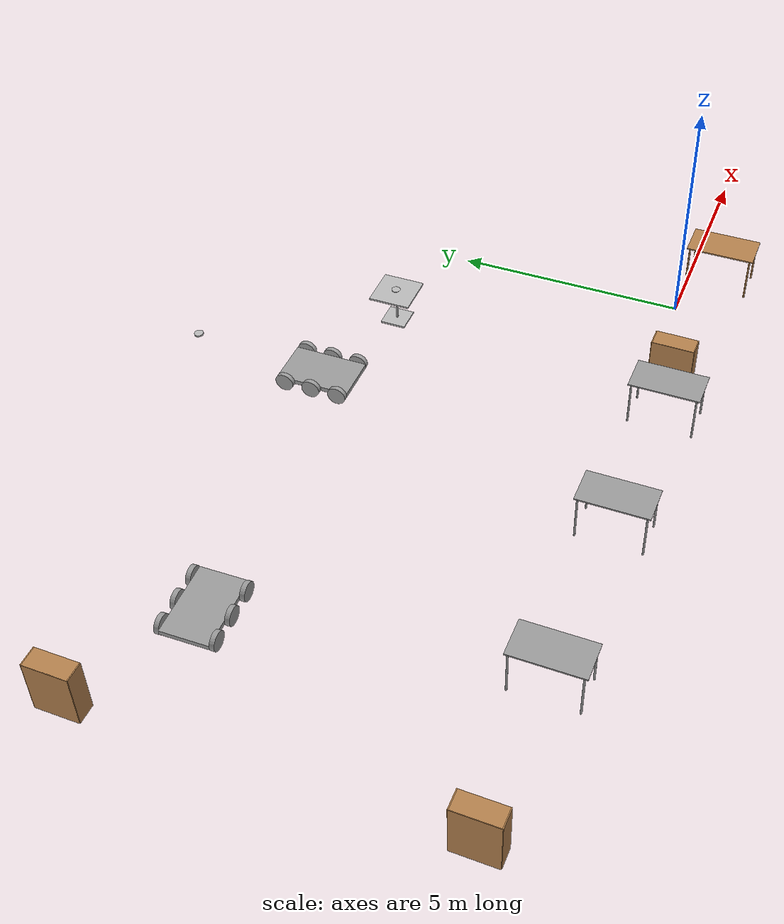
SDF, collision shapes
<?xml version='1.0'?>
<sdf version='1.6'>
  <model name='table_clone'>
    <link name='link'>
      <pose frame=''>1.35779 -0.669989 0 0 -0 1.5651</pose>
      <self_collide>0</self_collide>
      <kinematic>0</kinematic>
      <visual name='visual1'>
        <pose frame=''>0 0 1 0 -0 0</pose>
        <geometry>
          <box>
            <size>1.5 0.8 0.03</size>
          </box>
        </geometry>
        <material>
          <script>
            <uri>file://media/materials/scripts/gazebo.material</uri>
            <name>Gazebo/Wood</name>
          </script>
          <shader type='pixel'/>
          <ambient>1 1 1 1</ambient>
          <diffuse>1 1 1 1</diffuse>
          <specular>0.2 0.2 0.2 1</specular>
          <emissive>0 0 0 1</emissive>
        </material>
        <transparency>0</transparency>
        <cast_shadows>1</cast_shadows>
      </visual>
      <visual name='front_left_leg'>
        <pose frame=''>0.68 0.38 0.5 0 -0 0</pose>
        <geometry>
          <cylinder>
            <radius>0.02</radius>
            <length>1</length>
          </cylinder>
        </geometry>
        <material>
          <script>
            <uri>file://media/materials/scripts/gazebo.material</uri>
            <name>Gazebo/Grey</name>
          </script>
          <shader type='pixel'/>
          <ambient>0.3 0.3 0.3 1</ambient>
          <diffuse>0.7 0.7 0.7 1</diffuse>
          <specular>0.01 0.01 0.01 1</specular>
          <emissive>0 0 0 1</emissive>
        </material>
        <transparency>0</transparency>
        <cast_shadows>1</cast_shadows>
      </visual>
      <visual name='front_right_leg'>
        <pose frame=''>0.68 -0.38 0.5 0 -0 0</pose>
        <geometry>
          <cylinder>
            <radius>0.02</radius>
            <length>1</length>
          </cylinder>
        </geometry>
        <material>
          <script>
            <uri>file://media/materials/scripts/gazebo.material</uri>
            <name>Gazebo/Grey</name>
          </script>
          <shader type='pixel'/>
          <ambient>0.3 0.3 0.3 1</ambient>
          <diffuse>0.7 0.7 0.7 1</diffuse>
          <specular>0.01 0.01 0.01 1</specular>
          <emissive>0 0 0 1</emissive>
        </material>
        <transparency>0</transparency>
        <cast_shadows>1</cast_shadows>
      </visual>
      <visual name='back_right_leg'>
        <pose frame=''>-0.68 -0.38 0.5 0 -0 0</pose>
        <geometry>
          <cylinder>
            <radius>0.02</radius>
            <length>1</length>
          </cylinder>
        </geometry>
        <material>
          <script>
            <uri>file://media/materials/scripts/gazebo.material</uri>
            <name>Gazebo/Grey</name>
          </script>
          <shader type='pixel'/>
          <ambient>0.3 0.3 0.3 1</ambient>
          <diffuse>0.7 0.7 0.7 1</diffuse>
          <specular>0.01 0.01 0.01 1</specular>
          <emissive>0 0 0 1</emissive>
        </material>
        <transparency>0</transparency>
        <cast_shadows>1</cast_shadows>
      </visual>
      <visual name='back_left_leg'>
        <pose frame=''>-0.68 0.38 0.5 0 -0 0</pose>
        <geometry>
          <cylinder>
            <radius>0.02</radius>
            <length>1</length>
          </cylinder>
        </geometry>
        <material>
          <script>
            <uri>file://media/materials/scripts/gazebo.material</uri>
            <name>Gazebo/Grey</name>
          </script>
          <shader type='pixel'/>
          <ambient>0.3 0.3 0.3 1</ambient>
          <diffuse>0.7 0.7 0.7 1</diffuse>
          <specular>0.01 0.01 0.01 1</specular>
          <emissive>0 0 0 1</emissive>
        </material>
        <transparency>0</transparency>
        <cast_shadows>1</cast_shadows>
      </visual>
      <collision name='surface'>
        <laser_retro>0</laser_retro>
        <max_contacts>10</max_contacts>
        <pose frame=''>0 0 1 0 -0 0</pose>
        <geometry>
          <box>
            <size>1.5 0.8 0.03</size>
          </box>
        </geometry>
        <surface>
          <friction>
            <ode>
              <mu>0.6</mu>
              <mu2>0.6</mu2>
              <fdir1>0 0 0</fdir1>
              <slip1>0</slip1>
              <slip2>0</slip2>
            </ode>
            <torsional>
              <coefficient>1</coefficient>
              <patch_radius>0</patch_radius>
              <surface_radius>0</surface_radius>
              <use_patch_radius>1</use_patch_radius>
              <ode>
                <slip>0</slip>
              </ode>
            </torsional>
          </friction>
          <bounce>
            <restitution_coefficient>0</restitution_coefficient>
            <threshold>1e+06</threshold>
          </bounce>
          <contact>
            <collide_without_contact>0</collide_without_contact>
            <collide_without_contact_bitmask>1</collide_without_contact_bitmask>
            <collide_bitmask>1</collide_bitmask>
            <ode>
              <soft_cfm>0</soft_cfm>
              <soft_erp>0.2</soft_erp>
              <kp>1e+13</kp>
              <kd>1</kd>
              <max_vel>0.01</max_vel>
              <min_depth>0</min_depth>
            </ode>
            <bullet>
              <split_impulse>1</split_impulse>
              <split_impulse_penetration_threshold>-0.01</split_impulse_penetration_threshold>
              <soft_cfm>0</soft_cfm>
              <soft_erp>0.2</soft_erp>
              <kp>1e+13</kp>
              <kd>1</kd>
            </bullet>
          </contact>
        </surface>
      </collision>
      <collision name='front_left_leg'>
        <laser_retro>0</laser_retro>
        <max_contacts>10</max_contacts>
        <pose frame=''>0.68 0.38 0.5 0 -0 0</pose>
        <geometry>
          <cylinder>
            <radius>0.02</radius>
            <length>1</length>
          </cylinder>
        </geometry>
        <surface>
          <friction>
            <ode>
              <mu>1</mu>
              <mu2>1</mu2>
              <fdir1>0 0 0</fdir1>
              <slip1>0</slip1>
              <slip2>0</slip2>
            </ode>
            <torsional>
              <coefficient>1</coefficient>
              <patch_radius>0</patch_radius>
              <surface_radius>0</surface_radius>
              <use_patch_radius>1</use_patch_radius>
              <ode>
                <slip>0</slip>
              </ode>
            </torsional>
          </friction>
          <bounce>
            <restitution_coefficient>0</restitution_coefficient>
            <threshold>1e+06</threshold>
          </bounce>
          <contact>
            <collide_without_contact>0</collide_without_contact>
            <collide_without_contact_bitmask>1</collide_without_contact_bitmask>
            <collide_bitmask>1</collide_bitmask>
            <ode>
              <soft_cfm>0</soft_cfm>
              <soft_erp>0.2</soft_erp>
              <kp>1e+13</kp>
              <kd>1</kd>
              <max_vel>0.01</max_vel>
              <min_depth>0</min_depth>
            </ode>
            <bullet>
              <split_impulse>1</split_impulse>
              <split_impulse_penetration_threshold>-0.01</split_impulse_penetration_threshold>
              <soft_cfm>0</soft_cfm>
              <soft_erp>0.2</soft_erp>
              <kp>1e+13</kp>
              <kd>1</kd>
            </bullet>
          </contact>
        </surface>
      </collision>
      <collision name='front_right_leg'>
        <laser_retro>0</laser_retro>
        <max_contacts>10</max_contacts>
        <pose frame=''>0.68 -0.38 0.5 0 -0 0</pose>
        <geometry>
          <cylinder>
            <radius>0.02</radius>
            <length>1</length>
          </cylinder>
        </geometry>
        <surface>
          <friction>
            <ode>
              <mu>1</mu>
              <mu2>1</mu2>
              <fdir1>0 0 0</fdir1>
              <slip1>0</slip1>
              <slip2>0</slip2>
            </ode>
            <torsional>
              <coefficient>1</coefficient>
              <patch_radius>0</patch_radius>
              <surface_radius>0</surface_radius>
              <use_patch_radius>1</use_patch_radius>
              <ode>
                <slip>0</slip>
              </ode>
            </torsional>
          </friction>
          <bounce>
            <restitution_coefficient>0</restitution_coefficient>
            <threshold>1e+06</threshold>
          </bounce>
          <contact>
            <collide_without_contact>0</collide_without_contact>
            <collide_without_contact_bitmask>1</collide_without_contact_bitmask>
            <collide_bitmask>1</collide_bitmask>
            <ode>
              <soft_cfm>0</soft_cfm>
              <soft_erp>0.2</soft_erp>
              <kp>1e+13</kp>
              <kd>1</kd>
              <max_vel>0.01</max_vel>
              <min_depth>0</min_depth>
            </ode>
            <bullet>
              <split_impulse>1</split_impulse>
              <split_impulse_penetration_threshold>-0.01</split_impulse_penetration_threshold>
              <soft_cfm>0</soft_cfm>
              <soft_erp>0.2</soft_erp>
              <kp>1e+13</kp>
              <kd>1</kd>
            </bullet>
          </contact>
        </surface>
      </collision>
      <collision name='back_right_leg'>
        <laser_retro>0</laser_retro>
        <max_contacts>10</max_contacts>
        <pose frame=''>-0.68 -0.38 0.5 0 -0 0</pose>
        <geometry>
          <cylinder>
            <radius>0.02</radius>
            <length>1</length>
          </cylinder>
        </geometry>
        <surface>
          <friction>
            <ode>
              <mu>1</mu>
              <mu2>1</mu2>
              <fdir1>0 0 0</fdir1>
              <slip1>0</slip1>
              <slip2>0</slip2>
            </ode>
            <torsional>
              <coefficient>1</coefficient>
              <patch_radius>0</patch_radius>
              <surface_radius>0</surface_radius>
              <use_patch_radius>1</use_patch_radius>
              <ode>
                <slip>0</slip>
              </ode>
            </torsional>
          </friction>
          <bounce>
            <restitution_coefficient>0</restitution_coefficient>
            <threshold>1e+06</threshold>
          </bounce>
          <contact>
            <collide_without_contact>0</collide_without_contact>
            <collide_without_contact_bitmask>1</collide_without_contact_bitmask>
            <collide_bitmask>1</collide_bitmask>
            <ode>
              <soft_cfm>0</soft_cfm>
              <soft_erp>0.2</soft_erp>
              <kp>1e+13</kp>
              <kd>1</kd>
              <max_vel>0.01</max_vel>
              <min_depth>0</min_depth>
            </ode>
            <bullet>
              <split_impulse>1</split_impulse>
              <split_impulse_penetration_threshold>-0.01</split_impulse_penetration_threshold>
              <soft_cfm>0</soft_cfm>
              <soft_erp>0.2</soft_erp>
              <kp>1e+13</kp>
              <kd>1</kd>
            </bullet>
          </contact>
        </surface>
      </collision>
      <collision name='back_left_leg'>
        <laser_retro>0</laser_retro>
        <max_contacts>10</max_contacts>
        <pose frame=''>-0.68 0.38 0.5 0 -0 0</pose>
        <geometry>
          <cylinder>
            <radius>0.02</radius>
            <length>1</length>
          </cylinder>
        </geometry>
        <surface>
          <friction>
            <ode>
              <mu>1</mu>
              <mu2>1</mu2>
              <fdir1>0 0 0</fdir1>
              <slip1>0</slip1>
              <slip2>0</slip2>
            </ode>
            <torsional>
              <coefficient>1</coefficient>
              <patch_radius>0</patch_radius>
              <surface_radius>0</surface_radius>
              <use_patch_radius>1</use_patch_radius>
              <ode>
                <slip>0</slip>
              </ode>
            </torsional>
          </friction>
          <bounce>
            <restitution_coefficient>0</restitution_coefficient>
            <threshold>1e+06</threshold>
          </bounce>
          <contact>
            <collide_without_contact>0</collide_without_contact>
            <collide_without_contact_bitmask>1</collide_without_contact_bitmask>
            <collide_bitmask>1</collide_bitmask>
            <ode>
              <soft_cfm>0</soft_cfm>
              <soft_erp>0.2</soft_erp>
              <kp>1e+13</kp>
              <kd>1</kd>
              <max_vel>0.01</max_vel>
              <min_depth>0</min_depth>
            </ode>
            <bullet>
              <split_impulse>1</split_impulse>
              <split_impulse_penetration_threshold>-0.01</split_impulse_penetration_threshold>
              <soft_cfm>0</soft_cfm>
              <soft_erp>0.2</soft_erp>
              <kp>1e+13</kp>
              <kd>1</kd>
            </bullet>
          </contact>
        </surface>
      </collision>
    </link>
    <link name='link_clone'>
      <pose frame=''>-3.54635 -0.664185 0 0 -0 1.5651</pose>
      <self_collide>0</self_collide>
      <kinematic>0</kinematic>
      <visual name='back_left_leg'>
        <pose frame=''>-0.68 0.38 0.5 0 -0 0</pose>
        <geometry>
          <cylinder>
            <radius>0.02</radius>
            <length>1</length>
          </cylinder>
        </geometry>
        <material>
          <script>
            <uri>file://media/materials/scripts/gazebo.material</uri>
            <name>Gazebo/Grey</name>
          </script>
          <shader type='pixel'/>
          <ambient>0.3 0.3 0.3 1</ambient>
          <diffuse>0.7 0.7 0.7 1</diffuse>
          <specular>0.01 0.01 0.01 1</specular>
          <emissive>0 0 0 1</emissive>
        </material>
        <transparency>0</transparency>
        <cast_shadows>1</cast_shadows>
      </visual>
      <visual name='back_right_leg'>
        <pose frame=''>-0.68 -0.38 0.5 0 -0 0</pose>
        <geometry>
          <cylinder>
            <radius>0.02</radius>
            <length>1</length>
          </cylinder>
        </geometry>
        <material>
          <script>
            <uri>file://media/materials/scripts/gazebo.material</uri>
            <name>Gazebo/Grey</name>
          </script>
          <shader type='pixel'/>
          <ambient>0.3 0.3 0.3 1</ambient>
          <diffuse>0.7 0.7 0.7 1</diffuse>
          <specular>0.01 0.01 0.01 1</specular>
          <emissive>0 0 0 1</emissive>
        </material>
        <transparency>0</transparency>
        <cast_shadows>1</cast_shadows>
      </visual>
      <visual name='front_right_leg'>
        <pose frame=''>0.68 -0.38 0.5 0 -0 0</pose>
        <geometry>
          <cylinder>
            <radius>0.02</radius>
            <length>1</length>
          </cylinder>
        </geometry>
        <material>
          <script>
            <uri>file://media/materials/scripts/gazebo.material</uri>
            <name>Gazebo/Grey</name>
          </script>
          <shader type='pixel'/>
          <ambient>0.3 0.3 0.3 1</ambient>
          <diffuse>0.7 0.7 0.7 1</diffuse>
          <specular>0.01 0.01 0.01 1</specular>
          <emissive>0 0 0 1</emissive>
        </material>
        <transparency>0</transparency>
        <cast_shadows>1</cast_shadows>
      </visual>
      <visual name='visual1'>
        <pose frame=''>0 0 1 0 -0 0</pose>
        <geometry>
          <box>
            <size>1.5 0.8 0.03</size>
          </box>
        </geometry>
        <material>
          <script>
            <uri>file://media/materials/scripts/gazebo.material</uri>
            <name>Gazebo/Wood</name>
          </script>
          <shader type='pixel'/>
          <ambient>1 1 1 1</ambient>
          <diffuse>1 1 1 1</diffuse>
          <specular>0.2 0.2 0.2 1</specular>
          <emissive>0 0 0 1</emissive>
        </material>
        <transparency>0</transparency>
        <cast_shadows>1</cast_shadows>
      </visual>
      <visual name='front_left_leg'>
        <pose frame=''>0.68 0.38 0.5 0 -0 0</pose>
        <geometry>
          <cylinder>
            <radius>0.02</radius>
            <length>1</length>
          </cylinder>
        </geometry>
        <material>
          <script>
            <uri>file://media/materials/scripts/gazebo.material</uri>
            <name>Gazebo/Grey</name>
          </script>
          <shader type='pixel'/>
          <ambient>0.3 0.3 0.3 1</ambient>
          <diffuse>0.7 0.7 0.7 1</diffuse>
          <specular>0.01 0.01 0.01 1</specular>
          <emissive>0 0 0 1</emissive>
        </material>
        <transparency>0</transparency>
        <cast_shadows>1</cast_shadows>
      </visual>
      <collision name='back_right_leg_0'>
        <laser_retro>0</laser_retro>
        <max_contacts>10</max_contacts>
        <pose frame=''>-0.68 -0.38 0.5 0 -0 0</pose>
        <geometry>
          <cylinder>
            <radius>0.02</radius>
            <length>1</length>
          </cylinder>
        </geometry>
        <surface>
          <friction>
            <ode>
              <mu>1</mu>
              <mu2>1</mu2>
              <fdir1>0 0 0</fdir1>
              <slip1>0</slip1>
              <slip2>0</slip2>
            </ode>
            <torsional>
              <coefficient>1</coefficient>
              <patch_radius>0</patch_radius>
              <surface_radius>0</surface_radius>
              <use_patch_radius>1</use_patch_radius>
              <ode>
                <slip>0</slip>
              </ode>
            </torsional>
          </friction>
          <bounce>
            <restitution_coefficient>0</restitution_coefficient>
            <threshold>1e+06</threshold>
          </bounce>
          <contact>
            <collide_without_contact>0</collide_without_contact>
            <collide_without_contact_bitmask>1</collide_without_contact_bitmask>
            <collide_bitmask>1</collide_bitmask>
            <ode>
              <soft_cfm>0</soft_cfm>
              <soft_erp>0.2</soft_erp>
              <kp>1e+13</kp>
              <kd>1</kd>
              <max_vel>0.01</max_vel>
              <min_depth>0</min_depth>
            </ode>
            <bullet>
              <split_impulse>1</split_impulse>
              <split_impulse_penetration_threshold>-0.01</split_impulse_penetration_threshold>
              <soft_cfm>0</soft_cfm>
              <soft_erp>0.2</soft_erp>
              <kp>1e+13</kp>
              <kd>1</kd>
            </bullet>
          </contact>
        </surface>
      </collision>
      <collision name='front_left_leg_0'>
        <laser_retro>0</laser_retro>
        <max_contacts>10</max_contacts>
        <pose frame=''>0.68 0.38 0.5 0 -0 0</pose>
        <geometry>
          <cylinder>
            <radius>0.02</radius>
            <length>1</length>
          </cylinder>
        </geometry>
        <surface>
          <friction>
            <ode>
              <mu>1</mu>
              <mu2>1</mu2>
              <fdir1>0 0 0</fdir1>
              <slip1>0</slip1>
              <slip2>0</slip2>
            </ode>
            <torsional>
              <coefficient>1</coefficient>
              <patch_radius>0</patch_radius>
              <surface_radius>0</surface_radius>
              <use_patch_radius>1</use_patch_radius>
              <ode>
                <slip>0</slip>
              </ode>
            </torsional>
          </friction>
          <bounce>
            <restitution_coefficient>0</restitution_coefficient>
            <threshold>1e+06</threshold>
          </bounce>
          <contact>
            <collide_without_contact>0</collide_without_contact>
            <collide_without_contact_bitmask>1</collide_without_contact_bitmask>
            <collide_bitmask>1</collide_bitmask>
            <ode>
              <soft_cfm>0</soft_cfm>
              <soft_erp>0.2</soft_erp>
              <kp>1e+13</kp>
              <kd>1</kd>
              <max_vel>0.01</max_vel>
              <min_depth>0</min_depth>
            </ode>
            <bullet>
              <split_impulse>1</split_impulse>
              <split_impulse_penetration_threshold>-0.01</split_impulse_penetration_threshold>
              <soft_cfm>0</soft_cfm>
              <soft_erp>0.2</soft_erp>
              <kp>1e+13</kp>
              <kd>1</kd>
            </bullet>
          </contact>
        </surface>
      </collision>
      <collision name='back_left_leg_0'>
        <laser_retro>0</laser_retro>
        <max_contacts>10</max_contacts>
        <pose frame=''>-0.68 0.38 0.5 0 -0 0</pose>
        <geometry>
          <cylinder>
            <radius>0.02</radius>
            <length>1</length>
          </cylinder>
        </geometry>
        <surface>
          <friction>
            <ode>
              <mu>1</mu>
              <mu2>1</mu2>
              <fdir1>0 0 0</fdir1>
              <slip1>0</slip1>
              <slip2>0</slip2>
            </ode>
            <torsional>
              <coefficient>1</coefficient>
              <patch_radius>0</patch_radius>
              <surface_radius>0</surface_radius>
              <use_patch_radius>1</use_patch_radius>
              <ode>
                <slip>0</slip>
              </ode>
            </torsional>
          </friction>
          <bounce>
            <restitution_coefficient>0</restitution_coefficient>
            <threshold>1e+06</threshold>
          </bounce>
          <contact>
            <collide_without_contact>0</collide_without_contact>
            <collide_without_contact_bitmask>1</collide_without_contact_bitmask>
            <collide_bitmask>1</collide_bitmask>
            <ode>
              <soft_cfm>0</soft_cfm>
              <soft_erp>0.2</soft_erp>
              <kp>1e+13</kp>
              <kd>1</kd>
              <max_vel>0.01</max_vel>
              <min_depth>0</min_depth>
            </ode>
            <bullet>
              <split_impulse>1</split_impulse>
              <split_impulse_penetration_threshold>-0.01</split_impulse_penetration_threshold>
              <soft_cfm>0</soft_cfm>
              <soft_erp>0.2</soft_erp>
              <kp>1e+13</kp>
              <kd>1</kd>
            </bullet>
          </contact>
        </surface>
      </collision>
      <collision name='surface'>
        <laser_retro>0</laser_retro>
        <max_contacts>10</max_contacts>
        <pose frame=''>0 0 1 0 -0 0</pose>
        <geometry>
          <box>
            <size>1.5 0.8 0.03</size>
          </box>
        </geometry>
        <surface>
          <friction>
            <ode>
              <mu>1</mu>
              <mu2>1</mu2>
              <fdir1>0 0 0</fdir1>
              <slip1>0</slip1>
              <slip2>0</slip2>
            </ode>
            <torsional>
              <coefficient>1</coefficient>
              <patch_radius>0</patch_radius>
              <surface_radius>0</surface_radius>
              <use_patch_radius>1</use_patch_radius>
              <ode>
                <slip>0</slip>
              </ode>
            </torsional>
          </friction>
          <bounce>
            <restitution_coefficient>0</restitution_coefficient>
            <threshold>1e+06</threshold>
          </bounce>
          <contact>
            <collide_without_contact>0</collide_without_contact>
            <collide_without_contact_bitmask>1</collide_without_contact_bitmask>
            <collide_bitmask>1</collide_bitmask>
            <ode>
              <soft_cfm>0</soft_cfm>
              <soft_erp>0.2</soft_erp>
              <kp>1e+13</kp>
              <kd>1</kd>
              <max_vel>0.01</max_vel>
              <min_depth>0</min_depth>
            </ode>
            <bullet>
              <split_impulse>1</split_impulse>
              <split_impulse_penetration_threshold>-0.01</split_impulse_penetration_threshold>
              <soft_cfm>0</soft_cfm>
              <soft_erp>0.2</soft_erp>
              <kp>1e+13</kp>
              <kd>1</kd>
            </bullet>
          </contact>
        </surface>
      </collision>
      <collision name='front_right_leg_0'>
        <laser_retro>0</laser_retro>
        <max_contacts>10</max_contacts>
        <pose frame=''>0.68 -0.38 0.5 0 -0 0</pose>
        <geometry>
          <cylinder>
            <radius>0.02</radius>
            <length>1</length>
          </cylinder>
        </geometry>
        <surface>
          <friction>
            <ode>
              <mu>1</mu>
              <mu2>1</mu2>
              <fdir1>0 0 0</fdir1>
              <slip1>0</slip1>
              <slip2>0</slip2>
            </ode>
            <torsional>
              <coefficient>1</coefficient>
              <patch_radius>0</patch_radius>
              <surface_radius>0</surface_radius>
              <use_patch_radius>1</use_patch_radius>
              <ode>
                <slip>0</slip>
              </ode>
            </torsional>
          </friction>
          <bounce>
            <restitution_coefficient>0</restitution_coefficient>
            <threshold>1e+06</threshold>
          </bounce>
          <contact>
            <collide_without_contact>0</collide_without_contact>
            <collide_without_contact_bitmask>1</collide_without_contact_bitmask>
            <collide_bitmask>1</collide_bitmask>
            <ode>
              <soft_cfm>0</soft_cfm>
              <soft_erp>0.2</soft_erp>
              <kp>1e+13</kp>
              <kd>1</kd>
              <max_vel>0.01</max_vel>
              <min_depth>0</min_depth>
            </ode>
            <bullet>
              <split_impulse>1</split_impulse>
              <split_impulse_penetration_threshold>-0.01</split_impulse_penetration_threshold>
              <soft_cfm>0</soft_cfm>
              <soft_erp>0.2</soft_erp>
              <kp>1e+13</kp>
              <kd>1</kd>
            </bullet>
          </contact>
        </surface>
      </collision>
    </link>
    <link name='link_clone_clone'>
      <pose frame=''>-6.978 -0.58302 0 0 -0 1.5651</pose>
      <self_collide>0</self_collide>
      <kinematic>0</kinematic>
      <visual name='front_right_leg'>
        <pose frame=''>0.68 -0.38 0.5 0 -0 0</pose>
        <geometry>
          <cylinder>
            <radius>0.02</radius>
            <length>1</length>
          </cylinder>
        </geometry>
        <material>
          <script>
            <uri>file://media/materials/scripts/gazebo.material</uri>
            <name>Gazebo/Grey</name>
          </script>
          <shader type='pixel'/>
          <ambient>0.3 0.3 0.3 1</ambient>
          <diffuse>0.7 0.7 0.7 1</diffuse>
          <specular>0.01 0.01 0.01 1</specular>
          <emissive>0 0 0 1</emissive>
        </material>
        <transparency>0</transparency>
        <cast_shadows>1</cast_shadows>
      </visual>
      <visual name='visual1'>
        <pose frame=''>0 0 1 0 -0 0</pose>
        <geometry>
          <box>
            <size>1.5 0.8 0.03</size>
          </box>
        </geometry>
        <material>
          <script>
            <uri>file://media/materials/scripts/gazebo.material</uri>
            <name>Gazebo/Wood</name>
          </script>
          <shader type='pixel'/>
          <ambient>1 1 1 1</ambient>
          <diffuse>1 1 1 1</diffuse>
          <specular>0.2 0.2 0.2 1</specular>
          <emissive>0 0 0 1</emissive>
        </material>
        <transparency>0</transparency>
        <cast_shadows>1</cast_shadows>
      </visual>
      <visual name='front_left_leg'>
        <pose frame=''>0.68 0.38 0.5 0 -0 0</pose>
        <geometry>
          <cylinder>
            <radius>0.02</radius>
            <length>1</length>
          </cylinder>
        </geometry>
        <material>
          <script>
            <uri>file://media/materials/scripts/gazebo.material</uri>
            <name>Gazebo/Grey</name>
          </script>
          <shader type='pixel'/>
          <ambient>0.3 0.3 0.3 1</ambient>
          <diffuse>0.7 0.7 0.7 1</diffuse>
          <specular>0.01 0.01 0.01 1</specular>
          <emissive>0 0 0 1</emissive>
        </material>
        <transparency>0</transparency>
        <cast_shadows>1</cast_shadows>
      </visual>
      <visual name='back_left_leg'>
        <pose frame=''>-0.68 0.38 0.5 0 -0 0</pose>
        <geometry>
          <cylinder>
            <radius>0.02</radius>
            <length>1</length>
          </cylinder>
        </geometry>
        <material>
          <script>
            <uri>file://media/materials/scripts/gazebo.material</uri>
            <name>Gazebo/Grey</name>
          </script>
          <shader type='pixel'/>
          <ambient>0.3 0.3 0.3 1</ambient>
          <diffuse>0.7 0.7 0.7 1</diffuse>
          <specular>0.01 0.01 0.01 1</specular>
          <emissive>0 0 0 1</emissive>
        </material>
        <transparency>0</transparency>
        <cast_shadows>1</cast_shadows>
      </visual>
      <visual name='back_right_leg'>
        <pose frame=''>-0.68 -0.38 0.5 0 -0 0</pose>
        <geometry>
          <cylinder>
            <radius>0.02</radius>
            <length>1</length>
          </cylinder>
        </geometry>
        <material>
          <script>
            <uri>file://media/materials/scripts/gazebo.material</uri>
            <name>Gazebo/Grey</name>
          </script>
          <shader type='pixel'/>
          <ambient>0.3 0.3 0.3 1</ambient>
          <diffuse>0.7 0.7 0.7 1</diffuse>
          <specular>0.01 0.01 0.01 1</specular>
          <emissive>0 0 0 1</emissive>
        </material>
        <transparency>0</transparency>
        <cast_shadows>1</cast_shadows>
      </visual>
      <collision name='back_right_leg_0'>
        <laser_retro>0</laser_retro>
        <max_contacts>10</max_contacts>
        <pose frame=''>-0.68 -0.38 0.5 0 -0 0</pose>
        <geometry>
          <cylinder>
            <radius>0.02</radius>
            <length>1</length>
          </cylinder>
        </geometry>
        <surface>
          <friction>
            <ode>
              <mu>1</mu>
              <mu2>1</mu2>
              <fdir1>0 0 0</fdir1>
              <slip1>0</slip1>
              <slip2>0</slip2>
            </ode>
            <torsional>
              <coefficient>1</coefficient>
              <patch_radius>0</patch_radius>
              <surface_radius>0</surface_radius>
              <use_patch_radius>1</use_patch_radius>
              <ode>
                <slip>0</slip>
              </ode>
            </torsional>
          </friction>
          <bounce>
            <restitution_coefficient>0</restitution_coefficient>
            <threshold>1e+06</threshold>
          </bounce>
          <contact>
            <collide_without_contact>0</collide_without_contact>
            <collide_without_contact_bitmask>1</collide_without_contact_bitmask>
            <collide_bitmask>1</collide_bitmask>
            <ode>
              <soft_cfm>0</soft_cfm>
              <soft_erp>0.2</soft_erp>
              <kp>1e+13</kp>
              <kd>1</kd>
              <max_vel>0.01</max_vel>
              <min_depth>0</min_depth>
            </ode>
            <bullet>
              <split_impulse>1</split_impulse>
              <split_impulse_penetration_threshold>-0.01</split_impulse_penetration_threshold>
              <soft_cfm>0</soft_cfm>
              <soft_erp>0.2</soft_erp>
              <kp>1e+13</kp>
              <kd>1</kd>
            </bullet>
          </contact>
        </surface>
      </collision>
      <collision name='front_left_leg_0'>
        <laser_retro>0</laser_retro>
        <max_contacts>10</max_contacts>
        <pose frame=''>0.68 0.38 0.5 0 -0 0</pose>
        <geometry>
          <cylinder>
            <radius>0.02</radius>
            <length>1</length>
          </cylinder>
        </geometry>
        <surface>
          <friction>
            <ode>
              <mu>1</mu>
              <mu2>1</mu2>
              <fdir1>0 0 0</fdir1>
              <slip1>0</slip1>
              <slip2>0</slip2>
            </ode>
            <torsional>
              <coefficient>1</coefficient>
              <patch_radius>0</patch_radius>
              <surface_radius>0</surface_radius>
              <use_patch_radius>1</use_patch_radius>
              <ode>
                <slip>0</slip>
              </ode>
            </torsional>
          </friction>
          <bounce>
            <restitution_coefficient>0</restitution_coefficient>
            <threshold>1e+06</threshold>
          </bounce>
          <contact>
            <collide_without_contact>0</collide_without_contact>
            <collide_without_contact_bitmask>1</collide_without_contact_bitmask>
            <collide_bitmask>1</collide_bitmask>
            <ode>
              <soft_cfm>0</soft_cfm>
              <soft_erp>0.2</soft_erp>
              <kp>1e+13</kp>
              <kd>1</kd>
              <max_vel>0.01</max_vel>
              <min_depth>0</min_depth>
            </ode>
            <bullet>
              <split_impulse>1</split_impulse>
              <split_impulse_penetration_threshold>-0.01</split_impulse_penetration_threshold>
              <soft_cfm>0</soft_cfm>
              <soft_erp>0.2</soft_erp>
              <kp>1e+13</kp>
              <kd>1</kd>
            </bullet>
          </contact>
        </surface>
      </collision>
      <collision name='back_left_leg_0'>
        <laser_retro>0</laser_retro>
        <max_contacts>10</max_contacts>
        <pose frame=''>-0.68 0.38 0.5 0 -0 0</pose>
        <geometry>
          <cylinder>
            <radius>0.02</radius>
            <length>1</length>
          </cylinder>
        </geometry>
        <surface>
          <friction>
            <ode>
              <mu>1</mu>
              <mu2>1</mu2>
              <fdir1>0 0 0</fdir1>
              <slip1>0</slip1>
              <slip2>0</slip2>
            </ode>
            <torsional>
              <coefficient>1</coefficient>
              <patch_radius>0</patch_radius>
              <surface_radius>0</surface_radius>
              <use_patch_radius>1</use_patch_radius>
              <ode>
                <slip>0</slip>
              </ode>
            </torsional>
          </friction>
          <bounce>
            <restitution_coefficient>0</restitution_coefficient>
            <threshold>1e+06</threshold>
          </bounce>
          <contact>
            <collide_without_contact>0</collide_without_contact>
            <collide_without_contact_bitmask>1</collide_without_contact_bitmask>
            <collide_bitmask>1</collide_bitmask>
            <ode>
              <soft_cfm>0</soft_cfm>
              <soft_erp>0.2</soft_erp>
              <kp>1e+13</kp>
              <kd>1</kd>
              <max_vel>0.01</max_vel>
              <min_depth>0</min_depth>
            </ode>
            <bullet>
              <split_impulse>1</split_impulse>
              <split_impulse_penetration_threshold>-0.01</split_impulse_penetration_threshold>
              <soft_cfm>0</soft_cfm>
              <soft_erp>0.2</soft_erp>
              <kp>1e+13</kp>
              <kd>1</kd>
            </bullet>
          </contact>
        </surface>
      </collision>
      <collision name='surface'>
        <laser_retro>0</laser_retro>
        <max_contacts>10</max_contacts>
        <pose frame=''>0 0 1 0 -0 0</pose>
        <geometry>
          <box>
            <size>1.5 0.8 0.03</size>
          </box>
        </geometry>
        <surface>
          <friction>
            <ode>
              <mu>1</mu>
              <mu2>1</mu2>
              <fdir1>0 0 0</fdir1>
              <slip1>0</slip1>
              <slip2>0</slip2>
            </ode>
            <torsional>
              <coefficient>1</coefficient>
              <patch_radius>0</patch_radius>
              <surface_radius>0</surface_radius>
              <use_patch_radius>1</use_patch_radius>
              <ode>
                <slip>0</slip>
              </ode>
            </torsional>
          </friction>
          <bounce>
            <restitution_coefficient>0</restitution_coefficient>
            <threshold>1e+06</threshold>
          </bounce>
          <contact>
            <collide_without_contact>0</collide_without_contact>
            <collide_without_contact_bitmask>1</collide_without_contact_bitmask>
            <collide_bitmask>1</collide_bitmask>
            <ode>
              <soft_cfm>0</soft_cfm>
              <soft_erp>0.2</soft_erp>
              <kp>1e+13</kp>
              <kd>1</kd>
              <max_vel>0.01</max_vel>
              <min_depth>0</min_depth>
            </ode>
            <bullet>
              <split_impulse>1</split_impulse>
              <split_impulse_penetration_threshold>-0.01</split_impulse_penetration_threshold>
              <soft_cfm>0</soft_cfm>
              <soft_erp>0.2</soft_erp>
              <kp>1e+13</kp>
              <kd>1</kd>
            </bullet>
          </contact>
        </surface>
      </collision>
      <collision name='front_right_leg_0'>
        <laser_retro>0</laser_retro>
        <max_contacts>10</max_contacts>
        <pose frame=''>0.68 -0.38 0.5 0 -0 0</pose>
        <geometry>
          <cylinder>
            <radius>0.02</radius>
            <length>1</length>
          </cylinder>
        </geometry>
        <surface>
          <friction>
            <ode>
              <mu>1</mu>
              <mu2>1</mu2>
              <fdir1>0 0 0</fdir1>
              <slip1>0</slip1>
              <slip2>0</slip2>
            </ode>
            <torsional>
              <coefficient>1</coefficient>
              <patch_radius>0</patch_radius>
              <surface_radius>0</surface_radius>
              <use_patch_radius>1</use_patch_radius>
              <ode>
                <slip>0</slip>
              </ode>
            </torsional>
          </friction>
          <bounce>
            <restitution_coefficient>0</restitution_coefficient>
            <threshold>1e+06</threshold>
          </bounce>
          <contact>
            <collide_without_contact>0</collide_without_contact>
            <collide_without_contact_bitmask>1</collide_without_contact_bitmask>
            <collide_bitmask>1</collide_bitmask>
            <ode>
              <soft_cfm>0</soft_cfm>
              <soft_erp>0.2</soft_erp>
              <kp>1e+13</kp>
              <kd>1</kd>
              <max_vel>0.01</max_vel>
              <min_depth>0</min_depth>
            </ode>
            <bullet>
              <split_impulse>1</split_impulse>
              <split_impulse_penetration_threshold>-0.01</split_impulse_penetration_threshold>
              <soft_cfm>0</soft_cfm>
              <soft_erp>0.2</soft_erp>
              <kp>1e+13</kp>
              <kd>1</kd>
            </bullet>
          </contact>
        </surface>
      </collision>
    </link>
    <link name='link_clone_clone_clone'>
      <pose frame=''>-10.8249 -0.546977 0 0 -0 1.5651</pose>
      <self_collide>0</self_collide>
      <kinematic>0</kinematic>
      <visual name='front_right_leg'>
        <pose frame=''>0.68 -0.38 0.5 0 -0 0</pose>
        <geometry>
          <cylinder>
            <radius>0.02</radius>
            <length>1</length>
          </cylinder>
        </geometry>
        <material>
          <script>
            <uri>file://media/materials/scripts/gazebo.material</uri>
            <name>Gazebo/Grey</name>
          </script>
          <shader type='pixel'/>
          <ambient>0.3 0.3 0.3 1</ambient>
          <diffuse>0.7 0.7 0.7 1</diffuse>
          <specular>0.01 0.01 0.01 1</specular>
          <emissive>0 0 0 1</emissive>
        </material>
        <transparency>0</transparency>
        <cast_shadows>1</cast_shadows>
      </visual>
      <visual name='visual1'>
        <pose frame=''>0 0 1 0 -0 0</pose>
        <geometry>
          <box>
            <size>1.5 0.8 0.03</size>
          </box>
        </geometry>
        <material>
          <script>
            <uri>file://media/materials/scripts/gazebo.material</uri>
            <name>Gazebo/Wood</name>
          </script>
          <shader type='pixel'/>
          <ambient>1 1 1 1</ambient>
          <diffuse>1 1 1 1</diffuse>
          <specular>0.2 0.2 0.2 1</specular>
          <emissive>0 0 0 1</emissive>
        </material>
        <transparency>0</transparency>
        <cast_shadows>1</cast_shadows>
      </visual>
      <visual name='front_left_leg'>
        <pose frame=''>0.68 0.38 0.5 0 -0 0</pose>
        <geometry>
          <cylinder>
            <radius>0.02</radius>
            <length>1</length>
          </cylinder>
        </geometry>
        <material>
          <script>
            <uri>file://media/materials/scripts/gazebo.material</uri>
            <name>Gazebo/Grey</name>
          </script>
          <shader type='pixel'/>
          <ambient>0.3 0.3 0.3 1</ambient>
          <diffuse>0.7 0.7 0.7 1</diffuse>
          <specular>0.01 0.01 0.01 1</specular>
          <emissive>0 0 0 1</emissive>
        </material>
        <transparency>0</transparency>
        <cast_shadows>1</cast_shadows>
      </visual>
      <visual name='back_left_leg'>
        <pose frame=''>-0.68 0.38 0.5 0 -0 0</pose>
        <geometry>
          <cylinder>
            <radius>0.02</radius>
            <length>1</length>
          </cylinder>
        </geometry>
        <material>
          <script>
            <uri>file://media/materials/scripts/gazebo.material</uri>
            <name>Gazebo/Grey</name>
          </script>
          <shader type='pixel'/>
          <ambient>0.3 0.3 0.3 1</ambient>
          <diffuse>0.7 0.7 0.7 1</diffuse>
          <specular>0.01 0.01 0.01 1</specular>
          <emissive>0 0 0 1</emissive>
        </material>
        <transparency>0</transparency>
        <cast_shadows>1</cast_shadows>
      </visual>
      <visual name='back_right_leg'>
        <pose frame=''>-0.68 -0.38 0.5 0 -0 0</pose>
        <geometry>
          <cylinder>
            <radius>0.02</radius>
            <length>1</length>
          </cylinder>
        </geometry>
        <material>
          <script>
            <uri>file://media/materials/scripts/gazebo.material</uri>
            <name>Gazebo/Grey</name>
          </script>
          <shader type='pixel'/>
          <ambient>0.3 0.3 0.3 1</ambient>
          <diffuse>0.7 0.7 0.7 1</diffuse>
          <specular>0.01 0.01 0.01 1</specular>
          <emissive>0 0 0 1</emissive>
        </material>
        <transparency>0</transparency>
        <cast_shadows>1</cast_shadows>
      </visual>
      <collision name='front_left_leg_0'>
        <laser_retro>0</laser_retro>
        <max_contacts>10</max_contacts>
        <pose frame=''>0.68 0.38 0.5 0 -0 0</pose>
        <geometry>
          <cylinder>
            <radius>0.02</radius>
            <length>1</length>
          </cylinder>
        </geometry>
        <surface>
          <friction>
            <ode>
              <mu>1</mu>
              <mu2>1</mu2>
              <fdir1>0 0 0</fdir1>
              <slip1>0</slip1>
              <slip2>0</slip2>
            </ode>
            <torsional>
              <coefficient>1</coefficient>
              <patch_radius>0</patch_radius>
              <surface_radius>0</surface_radius>
              <use_patch_radius>1</use_patch_radius>
              <ode>
                <slip>0</slip>
              </ode>
            </torsional>
          </friction>
          <bounce>
            <restitution_coefficient>0</restitution_coefficient>
            <threshold>1e+06</threshold>
          </bounce>
          <contact>
            <collide_without_contact>0</collide_without_contact>
            <collide_without_contact_bitmask>1</collide_without_contact_bitmask>
            <collide_bitmask>1</collide_bitmask>
            <ode>
              <soft_cfm>0</soft_cfm>
              <soft_erp>0.2</soft_erp>
              <kp>1e+13</kp>
              <kd>1</kd>
              <max_vel>0.01</max_vel>
              <min_depth>0</min_depth>
            </ode>
            <bullet>
              <split_impulse>1</split_impulse>
              <split_impulse_penetration_threshold>-0.01</split_impulse_penetration_threshold>
              <soft_cfm>0</soft_cfm>
              <soft_erp>0.2</soft_erp>
              <kp>1e+13</kp>
              <kd>1</kd>
            </bullet>
          </contact>
        </surface>
      </collision>
      <collision name='back_right_leg_0'>
        <laser_retro>0</laser_retro>
        <max_contacts>10</max_contacts>
        <pose frame=''>-0.68 -0.38 0.5 0 -0 0</pose>
        <geometry>
          <cylinder>
            <radius>0.02</radius>
            <length>1</length>
          </cylinder>
        </geometry>
        <surface>
          <friction>
            <ode>
              <mu>1</mu>
              <mu2>1</mu2>
              <fdir1>0 0 0</fdir1>
              <slip1>0</slip1>
              <slip2>0</slip2>
            </ode>
            <torsional>
              <coefficient>1</coefficient>
              <patch_radius>0</patch_radius>
              <surface_radius>0</surface_radius>
              <use_patch_radius>1</use_patch_radius>
              <ode>
                <slip>0</slip>
              </ode>
            </torsional>
          </friction>
          <bounce>
            <restitution_coefficient>0</restitution_coefficient>
            <threshold>1e+06</threshold>
          </bounce>
          <contact>
            <collide_without_contact>0</collide_without_contact>
            <collide_without_contact_bitmask>1</collide_without_contact_bitmask>
            <collide_bitmask>1</collide_bitmask>
            <ode>
              <soft_cfm>0</soft_cfm>
              <soft_erp>0.2</soft_erp>
              <kp>1e+13</kp>
              <kd>1</kd>
              <max_vel>0.01</max_vel>
              <min_depth>0</min_depth>
            </ode>
            <bullet>
              <split_impulse>1</split_impulse>
              <split_impulse_penetration_threshold>-0.01</split_impulse_penetration_threshold>
              <soft_cfm>0</soft_cfm>
              <soft_erp>0.2</soft_erp>
              <kp>1e+13</kp>
              <kd>1</kd>
            </bullet>
          </contact>
        </surface>
      </collision>
      <collision name='back_left_leg_0'>
        <laser_retro>0</laser_retro>
        <max_contacts>10</max_contacts>
        <pose frame=''>-0.68 0.38 0.5 0 -0 0</pose>
        <geometry>
          <cylinder>
            <radius>0.02</radius>
            <length>1</length>
          </cylinder>
        </geometry>
        <surface>
          <friction>
            <ode>
              <mu>1</mu>
              <mu2>1</mu2>
              <fdir1>0 0 0</fdir1>
              <slip1>0</slip1>
              <slip2>0</slip2>
            </ode>
            <torsional>
              <coefficient>1</coefficient>
              <patch_radius>0</patch_radius>
              <surface_radius>0</surface_radius>
              <use_patch_radius>1</use_patch_radius>
              <ode>
                <slip>0</slip>
              </ode>
            </torsional>
          </friction>
          <bounce>
            <restitution_coefficient>0</restitution_coefficient>
            <threshold>1e+06</threshold>
          </bounce>
          <contact>
            <collide_without_contact>0</collide_without_contact>
            <collide_without_contact_bitmask>1</collide_without_contact_bitmask>
            <collide_bitmask>1</collide_bitmask>
            <ode>
              <soft_cfm>0</soft_cfm>
              <soft_erp>0.2</soft_erp>
              <kp>1e+13</kp>
              <kd>1</kd>
              <max_vel>0.01</max_vel>
              <min_depth>0</min_depth>
            </ode>
            <bullet>
              <split_impulse>1</split_impulse>
              <split_impulse_penetration_threshold>-0.01</split_impulse_penetration_threshold>
              <soft_cfm>0</soft_cfm>
              <soft_erp>0.2</soft_erp>
              <kp>1e+13</kp>
              <kd>1</kd>
            </bullet>
          </contact>
        </surface>
      </collision>
      <collision name='surface'>
        <laser_retro>0</laser_retro>
        <max_contacts>10</max_contacts>
        <pose frame=''>0 0 1 0 -0 0</pose>
        <geometry>
          <box>
            <size>1.5 0.8 0.03</size>
          </box>
        </geometry>
        <surface>
          <friction>
            <ode>
              <mu>1</mu>
              <mu2>1</mu2>
              <fdir1>0 0 0</fdir1>
              <slip1>0</slip1>
              <slip2>0</slip2>
            </ode>
            <torsional>
              <coefficient>1</coefficient>
              <patch_radius>0</patch_radius>
              <surface_radius>0</surface_radius>
              <use_patch_radius>1</use_patch_radius>
              <ode>
                <slip>0</slip>
              </ode>
            </torsional>
          </friction>
          <bounce>
            <restitution_coefficient>0</restitution_coefficient>
            <threshold>1e+06</threshold>
          </bounce>
          <contact>
            <collide_without_contact>0</collide_without_contact>
            <collide_without_contact_bitmask>1</collide_without_contact_bitmask>
            <collide_bitmask>1</collide_bitmask>
            <ode>
              <soft_cfm>0</soft_cfm>
              <soft_erp>0.2</soft_erp>
              <kp>1e+13</kp>
              <kd>1</kd>
              <max_vel>0.01</max_vel>
              <min_depth>0</min_depth>
            </ode>
            <bullet>
              <split_impulse>1</split_impulse>
              <split_impulse_penetration_threshold>-0.01</split_impulse_penetration_threshold>
              <soft_cfm>0</soft_cfm>
              <soft_erp>0.2</soft_erp>
              <kp>1e+13</kp>
              <kd>1</kd>
            </bullet>
          </contact>
        </surface>
      </collision>
      <collision name='front_right_leg_0'>
        <laser_retro>0</laser_retro>
        <max_contacts>10</max_contacts>
        <pose frame=''>0.68 -0.38 0.5 0 -0 0</pose>
        <geometry>
          <cylinder>
            <radius>0.02</radius>
            <length>1</length>
          </cylinder>
        </geometry>
        <surface>
          <friction>
            <ode>
              <mu>1</mu>
              <mu2>1</mu2>
              <fdir1>0 0 0</fdir1>
              <slip1>0</slip1>
              <slip2>0</slip2>
            </ode>
            <torsional>
              <coefficient>1</coefficient>
              <patch_radius>0</patch_radius>
              <surface_radius>0</surface_radius>
              <use_patch_radius>1</use_patch_radius>
              <ode>
                <slip>0</slip>
              </ode>
            </torsional>
          </friction>
          <bounce>
            <restitution_coefficient>0</restitution_coefficient>
            <threshold>1e+06</threshold>
          </bounce>
          <contact>
            <collide_without_contact>0</collide_without_contact>
            <collide_without_contact_bitmask>1</collide_without_contact_bitmask>
            <collide_bitmask>1</collide_bitmask>
            <ode>
              <soft_cfm>0</soft_cfm>
              <soft_erp>0.2</soft_erp>
              <kp>1e+13</kp>
              <kd>1</kd>
              <max_vel>0.01</max_vel>
              <min_depth>0</min_depth>
            </ode>
            <bullet>
              <split_impulse>1</split_impulse>
              <split_impulse_penetration_threshold>-0.01</split_impulse_penetration_threshold>
              <soft_cfm>0</soft_cfm>
              <soft_erp>0.2</soft_erp>
              <kp>1e+13</kp>
              <kd>1</kd>
            </bullet>
          </contact>
        </surface>
      </collision>
    </link>
    <model name='P1Model'>
      <link name='link_5'>
        <pose frame=''>0 0 -8e-06 0 -0 0</pose>
        <inertial>
          <mass>1</mass>
          <inertia>
            <ixx>0.166667</ixx>
            <ixy>0</ixy>
            <ixz>0</ixz>
            <iyy>0.166667</iyy>
            <iyz>0</iyz>
            <izz>0.166667</izz>
          </inertia>
          <pose frame=''>0 0 0 0 -0 0</pose>
        </inertial>
        <gravity>1</gravity>
        <self_collide>0</self_collide>
        <kinematic>0</kinematic>
        <visual name='visual'>
          <pose frame=''>0 0 0 0 -0 0</pose>
          <geometry>
            <box>
              <size>1.6 1 0.1</size>
            </box>
          </geometry>
          <material>
            <lighting>1</lighting>
            <script>
              <uri>file://media/materials/scripts/gazebo.material</uri>
              <name>Gazebo/Grey</name>
            </script>
            <shader type='pixel'>
              <normal_map>__default__</normal_map>
            </shader>
            <ambient>0.3 0.3 0.3 1</ambient>
            <diffuse>0.7 0.7 0.7 1</diffuse>
            <specular>0.01 0.01 0.01 1</specular>
            <emissive>0 0 0 1</emissive>
          </material>
          <transparency>0</transparency>
          <cast_shadows>1</cast_shadows>
        </visual>
        <collision name='collision'>
          <laser_retro>0</laser_retro>
          <max_contacts>10</max_contacts>
          <pose frame=''>0 0 0 0 -0 0</pose>
          <geometry>
            <box>
              <size>1.6 1 0.1</size>
            </box>
          </geometry>
          <surface>
            <friction>
              <ode>
                <mu>1</mu>
                <mu2>1</mu2>
                <fdir1>0 0 0</fdir1>
                <slip1>0</slip1>
                <slip2>0</slip2>
              </ode>
              <torsional>
                <coefficient>1</coefficient>
                <patch_radius>0</patch_radius>
                <surface_radius>0</surface_radius>
                <use_patch_radius>1</use_patch_radius>
                <ode>
                  <slip>0</slip>
                </ode>
              </torsional>
            </friction>
            <bounce>
              <restitution_coefficient>0</restitution_coefficient>
              <threshold>1e+06</threshold>
            </bounce>
            <contact>
              <collide_without_contact>0</collide_without_contact>
              <collide_without_contact_bitmask>1</collide_without_contact_bitmask>
              <collide_bitmask>1</collide_bitmask>
              <ode>
                <soft_cfm>0</soft_cfm>
                <soft_erp>0.2</soft_erp>
                <kp>1e+13</kp>
                <kd>1</kd>
                <max_vel>0.01</max_vel>
                <min_depth>0</min_depth>
              </ode>
              <bullet>
                <split_impulse>1</split_impulse>
                <split_impulse_penetration_threshold>-0.01</split_impulse_penetration_threshold>
                <soft_cfm>0</soft_cfm>
                <soft_erp>0.2</soft_erp>
                <kp>1e+13</kp>
                <kd>1</kd>
              </bullet>
            </contact>
          </surface>
        </collision>
      </link>
      <link name='link_6'>
        <pose frame=''>0 -0.550019 -8e-06 1.5707 -0 0</pose>
        <inertial>
          <mass>1</mass>
          <inertia>
            <ixx>0.145833</ixx>
            <ixy>0</ixy>
            <ixz>0</ixz>
            <iyy>0.145833</iyy>
            <iyz>0</iyz>
            <izz>0.125</izz>
          </inertia>
          <pose frame=''>0 0 0 0 -0 0</pose>
        </inertial>
        <gravity>1</gravity>
        <self_collide>0</self_collide>
        <kinematic>0</kinematic>
        <visual name='visual'>
          <pose frame=''>0 0 0 0 -0 0</pose>
          <geometry>
            <cylinder>
              <radius>0.2</radius>
              <length>0.1</length>
            </cylinder>
          </geometry>
          <material>
            <lighting>1</lighting>
            <script>
              <uri>file://media/materials/scripts/gazebo.material</uri>
              <name>Gazebo/Grey</name>
            </script>
            <shader type='pixel'>
              <normal_map>__default__</normal_map>
            </shader>
            <ambient>0.3 0.3 0.3 1</ambient>
            <diffuse>0.7 0.7 0.7 1</diffuse>
            <specular>0.01 0.01 0.01 1</specular>
            <emissive>0 0 0 1</emissive>
          </material>
          <transparency>0</transparency>
          <cast_shadows>1</cast_shadows>
        </visual>
        <collision name='collision'>
          <laser_retro>0</laser_retro>
          <max_contacts>10</max_contacts>
          <pose frame=''>0 0 0 0 -0 0</pose>
          <geometry>
            <cylinder>
              <radius>0.2</radius>
              <length>0.1</length>
            </cylinder>
          </geometry>
          <surface>
            <friction>
              <ode>
                <mu>1</mu>
                <mu2>1</mu2>
                <fdir1>0 0 0</fdir1>
                <slip1>0</slip1>
                <slip2>0</slip2>
              </ode>
              <torsional>
                <coefficient>1</coefficient>
                <patch_radius>0</patch_radius>
                <surface_radius>0</surface_radius>
                <use_patch_radius>1</use_patch_radius>
                <ode>
                  <slip>0</slip>
                </ode>
              </torsional>
            </friction>
            <bounce>
              <restitution_coefficient>0</restitution_coefficient>
              <threshold>1e+06</threshold>
            </bounce>
            <contact>
              <collide_without_contact>0</collide_without_contact>
              <collide_without_contact_bitmask>1</collide_without_contact_bitmask>
              <collide_bitmask>1</collide_bitmask>
              <ode>
                <soft_cfm>0</soft_cfm>
                <soft_erp>0.2</soft_erp>
                <kp>1e+13</kp>
                <kd>1</kd>
                <max_vel>0.01</max_vel>
                <min_depth>0</min_depth>
              </ode>
              <bullet>
                <split_impulse>1</split_impulse>
                <split_impulse_penetration_threshold>-0.01</split_impulse_penetration_threshold>
                <soft_cfm>0</soft_cfm>
                <soft_erp>0.2</soft_erp>
                <kp>1e+13</kp>
                <kd>1</kd>
              </bullet>
            </contact>
          </surface>
        </collision>
      </link>
      <link name='link_6_clone'>
        <pose frame=''>0 0.550019 -8e-06 1.5707 -0 0</pose>
        <inertial>
          <mass>1</mass>
          <inertia>
            <ixx>0.145833</ixx>
            <ixy>0</ixy>
            <ixz>0</ixz>
            <iyy>0.145833</iyy>
            <iyz>0</iyz>
            <izz>0.125</izz>
          </inertia>
          <pose frame=''>0 0 0 0 -0 0</pose>
        </inertial>
        <self_collide>0</self_collide>
        <kinematic>0</kinematic>
        <gravity>1</gravity>
        <visual name='visual'>
          <pose frame=''>0 0 0 0 -0 0</pose>
          <geometry>
            <cylinder>
              <radius>0.2</radius>
              <length>0.1</length>
            </cylinder>
          </geometry>
          <material>
            <lighting>1</lighting>
            <script>
              <uri>file://media/materials/scripts/gazebo.material</uri>
              <name>Gazebo/Grey</name>
            </script>
            <shader type='pixel'>
              <normal_map>__default__</normal_map>
            </shader>
            <ambient>0.3 0.3 0.3 1</ambient>
            <diffuse>0.7 0.7 0.7 1</diffuse>
            <specular>0.01 0.01 0.01 1</specular>
            <emissive>0 0 0 1</emissive>
          </material>
          <transparency>0</transparency>
          <cast_shadows>1</cast_shadows>
        </visual>
        <collision name='collision'>
          <laser_retro>0</laser_retro>
          <max_contacts>10</max_contacts>
          <pose frame=''>0 0 0 0 -0 0</pose>
          <geometry>
            <cylinder>
              <radius>0.2</radius>
              <length>0.1</length>
            </cylinder>
          </geometry>
          <surface>
            <friction>
              <ode>
                <mu>1</mu>
                <mu2>1</mu2>
                <fdir1>0 0 0</fdir1>
                <slip1>0</slip1>
                <slip2>0</slip2>
              </ode>
              <torsional>
                <coefficient>1</coefficient>
                <patch_radius>0</patch_radius>
                <surface_radius>0</surface_radius>
                <use_patch_radius>1</use_patch_radius>
                <ode>
                  <slip>0</slip>
                </ode>
              </torsional>
            </friction>
            <bounce>
              <restitution_coefficient>0</restitution_coefficient>
              <threshold>1e+06</threshold>
            </bounce>
            <contact>
              <collide_without_contact>0</collide_without_contact>
              <collide_without_contact_bitmask>1</collide_without_contact_bitmask>
              <collide_bitmask>1</collide_bitmask>
              <ode>
                <soft_cfm>0</soft_cfm>
                <soft_erp>0.2</soft_erp>
                <kp>1e+13</kp>
                <kd>1</kd>
                <max_vel>0.01</max_vel>
                <min_depth>0</min_depth>
              </ode>
              <bullet>
                <split_impulse>1</split_impulse>
                <split_impulse_penetration_threshold>-0.01</split_impulse_penetration_threshold>
                <soft_cfm>0</soft_cfm>
                <soft_erp>0.2</soft_erp>
                <kp>1e+13</kp>
                <kd>1</kd>
              </bullet>
            </contact>
          </surface>
        </collision>
      </link>
      <link name='link_6_clone_clone'>
        <pose frame=''>-0.6 -0.550019 -8e-06 1.5707 -0 0</pose>
        <inertial>
          <mass>1</mass>
          <inertia>
            <ixx>0.145833</ixx>
            <ixy>0</ixy>
            <ixz>0</ixz>
            <iyy>0.145833</iyy>
            <iyz>0</iyz>
            <izz>0.125</izz>
          </inertia>
          <pose frame=''>0 0 0 0 -0 0</pose>
        </inertial>
        <self_collide>0</self_collide>
        <kinematic>0</kinematic>
        <gravity>1</gravity>
        <visual name='visual'>
          <pose frame=''>0 0 0 0 -0 0</pose>
          <geometry>
            <cylinder>
              <radius>0.2</radius>
              <length>0.1</length>
            </cylinder>
          </geometry>
          <material>
            <lighting>1</lighting>
            <script>
              <uri>file://media/materials/scripts/gazebo.material</uri>
              <name>Gazebo/Grey</name>
            </script>
            <shader type='pixel'>
              <normal_map>__default__</normal_map>
            </shader>
            <ambient>0.3 0.3 0.3 1</ambient>
            <diffuse>0.7 0.7 0.7 1</diffuse>
            <specular>0.01 0.01 0.01 1</specular>
            <emissive>0 0 0 1</emissive>
          </material>
          <transparency>0</transparency>
          <cast_shadows>1</cast_shadows>
        </visual>
        <collision name='collision'>
          <laser_retro>0</laser_retro>
          <max_contacts>10</max_contacts>
          <pose frame=''>0 0 0 0 -0 0</pose>
          <geometry>
            <cylinder>
              <radius>0.2</radius>
              <length>0.1</length>
            </cylinder>
          </geometry>
          <surface>
            <friction>
              <ode>
                <mu>1</mu>
                <mu2>1</mu2>
                <fdir1>0 0 0</fdir1>
                <slip1>0</slip1>
                <slip2>0</slip2>
              </ode>
              <torsional>
                <coefficient>1</coefficient>
                <patch_radius>0</patch_radius>
                <surface_radius>0</surface_radius>
                <use_patch_radius>1</use_patch_radius>
                <ode>
                  <slip>0</slip>
                </ode>
              </torsional>
            </friction>
            <bounce>
              <restitution_coefficient>0</restitution_coefficient>
              <threshold>1e+06</threshold>
            </bounce>
            <contact>
              <collide_without_contact>0</collide_without_contact>
              <collide_without_contact_bitmask>1</collide_without_contact_bitmask>
              <collide_bitmask>1</collide_bitmask>
              <ode>
                <soft_cfm>0</soft_cfm>
                <soft_erp>0.2</soft_erp>
                <kp>1e+13</kp>
                <kd>1</kd>
                <max_vel>0.01</max_vel>
                <min_depth>0</min_depth>
              </ode>
              <bullet>
                <split_impulse>1</split_impulse>
                <split_impulse_penetration_threshold>-0.01</split_impulse_penetration_threshold>
                <soft_cfm>0</soft_cfm>
                <soft_erp>0.2</soft_erp>
                <kp>1e+13</kp>
                <kd>1</kd>
              </bullet>
            </contact>
          </surface>
        </collision>
      </link>
      <link name='link_6_clone_clone_0'>
        <pose frame=''>0.6 0.550019 -8e-06 1.5707 -0 0</pose>
        <inertial>
          <mass>1</mass>
          <inertia>
            <ixx>0.145833</ixx>
            <ixy>0</ixy>
            <ixz>0</ixz>
            <iyy>0.145833</iyy>
            <iyz>0</iyz>
            <izz>0.125</izz>
          </inertia>
          <pose frame=''>0 0 0 0 -0 0</pose>
        </inertial>
        <self_collide>0</self_collide>
        <kinematic>0</kinematic>
        <visual name='visual'>
          <pose frame=''>0 0 0 0 -0 0</pose>
          <geometry>
            <cylinder>
              <radius>0.2</radius>
              <length>0.1</length>
            </cylinder>
          </geometry>
          <material>
            <lighting>1</lighting>
            <script>
              <uri>file://media/materials/scripts/gazebo.material</uri>
              <name>Gazebo/Grey</name>
            </script>
            <shader type='pixel'>
              <normal_map>__default__</normal_map>
            </shader>
            <ambient>0.3 0.3 0.3 1</ambient>
            <diffuse>0.7 0.7 0.7 1</diffuse>
            <specular>0.01 0.01 0.01 1</specular>
            <emissive>0 0 0 1</emissive>
          </material>
          <transparency>0</transparency>
          <cast_shadows>1</cast_shadows>
        </visual>
        <collision name='collision'>
          <laser_retro>0</laser_retro>
          <max_contacts>10</max_contacts>
          <pose frame=''>0 0 0 0 -0 0</pose>
          <geometry>
            <cylinder>
              <radius>0.2</radius>
              <length>0.1</length>
            </cylinder>
          </geometry>
          <surface>
            <friction>
              <ode>
                <mu>1</mu>
                <mu2>1</mu2>
                <fdir1>0 0 0</fdir1>
                <slip1>0</slip1>
                <slip2>0</slip2>
              </ode>
              <torsional>
                <coefficient>1</coefficient>
                <patch_radius>0</patch_radius>
                <surface_radius>0</surface_radius>
                <use_patch_radius>1</use_patch_radius>
                <ode>
                  <slip>0</slip>
                </ode>
              </torsional>
            </friction>
            <bounce>
              <restitution_coefficient>0</restitution_coefficient>
              <threshold>1e+06</threshold>
            </bounce>
            <contact>
              <collide_without_contact>0</collide_without_contact>
              <collide_without_contact_bitmask>1</collide_without_contact_bitmask>
              <collide_bitmask>1</collide_bitmask>
              <ode>
                <soft_cfm>0</soft_cfm>
                <soft_erp>0.2</soft_erp>
                <kp>1e+13</kp>
                <kd>1</kd>
                <max_vel>0.01</max_vel>
                <min_depth>0</min_depth>
              </ode>
              <bullet>
                <split_impulse>1</split_impulse>
                <split_impulse_penetration_threshold>-0.01</split_impulse_penetration_threshold>
                <soft_cfm>0</soft_cfm>
                <soft_erp>0.2</soft_erp>
                <kp>1e+13</kp>
                <kd>1</kd>
              </bullet>
            </contact>
          </surface>
        </collision>
      </link>
      <link name='link_6_clone_clone_1'>
        <pose frame=''>-0.6 0.550019 4.8e-05 1.5707 -0 0</pose>
        <inertial>
          <mass>1</mass>
          <inertia>
            <ixx>0.145833</ixx>
            <ixy>0</ixy>
            <ixz>0</ixz>
            <iyy>0.145833</iyy>
            <iyz>0</iyz>
            <izz>0.125</izz>
          </inertia>
          <pose frame=''>0 0 0 0 -0 0</pose>
        </inertial>
        <self_collide>0</self_collide>
        <kinematic>0</kinematic>
        <visual name='visual'>
          <pose frame=''>0 0 0 0 -0 0</pose>
          <geometry>
            <cylinder>
              <radius>0.2</radius>
              <length>0.1</length>
            </cylinder>
          </geometry>
          <material>
            <lighting>1</lighting>
            <script>
              <uri>file://media/materials/scripts/gazebo.material</uri>
              <name>Gazebo/Grey</name>
            </script>
            <shader type='pixel'>
              <normal_map>__default__</normal_map>
            </shader>
            <ambient>0.3 0.3 0.3 1</ambient>
            <diffuse>0.7 0.7 0.7 1</diffuse>
            <specular>0.01 0.01 0.01 1</specular>
            <emissive>0 0 0 1</emissive>
          </material>
          <transparency>0</transparency>
          <cast_shadows>1</cast_shadows>
        </visual>
        <collision name='collision'>
          <laser_retro>0</laser_retro>
          <max_contacts>10</max_contacts>
          <pose frame=''>0 0 0 0 -0 0</pose>
          <geometry>
            <cylinder>
              <radius>0.2</radius>
              <length>0.1</length>
            </cylinder>
          </geometry>
          <surface>
            <friction>
              <ode>
                <mu>1</mu>
                <mu2>1</mu2>
                <fdir1>0 0 0</fdir1>
                <slip1>0</slip1>
                <slip2>0</slip2>
              </ode>
              <torsional>
                <coefficient>1</coefficient>
                <patch_radius>0</patch_radius>
                <surface_radius>0</surface_radius>
                <use_patch_radius>1</use_patch_radius>
                <ode>
                  <slip>0</slip>
                </ode>
              </torsional>
            </friction>
            <bounce>
              <restitution_coefficient>0</restitution_coefficient>
              <threshold>1e+06</threshold>
            </bounce>
            <contact>
              <collide_without_contact>0</collide_without_contact>
              <collide_without_contact_bitmask>1</collide_without_contact_bitmask>
              <collide_bitmask>1</collide_bitmask>
              <ode>
                <soft_cfm>0</soft_cfm>
                <soft_erp>0.2</soft_erp>
                <kp>1e+13</kp>
                <kd>1</kd>
                <max_vel>0.01</max_vel>
                <min_depth>0</min_depth>
              </ode>
              <bullet>
                <split_impulse>1</split_impulse>
                <split_impulse_penetration_threshold>-0.01</split_impulse_penetration_threshold>
                <soft_cfm>0</soft_cfm>
                <soft_erp>0.2</soft_erp>
                <kp>1e+13</kp>
                <kd>1</kd>
              </bullet>
            </contact>
          </surface>
        </collision>
      </link>
      <link name='link_6_clone_clone_1_clone'>
        <pose frame=''>0.6 -0.550019 -8e-06 1.5707 -0 0</pose>
        <inertial>
          <mass>1</mass>
          <inertia>
            <ixx>0.145833</ixx>
            <ixy>0</ixy>
            <ixz>0</ixz>
            <iyy>0.145833</iyy>
            <iyz>0</iyz>
            <izz>0.125</izz>
          </inertia>
          <pose frame=''>0 0 0 0 -0 0</pose>
        </inertial>
        <self_collide>0</self_collide>
        <kinematic>0</kinematic>
        <visual name='visual'>
          <pose frame=''>0 0 0 0 -0 0</pose>
          <geometry>
            <cylinder>
              <radius>0.2</radius>
              <length>0.1</length>
            </cylinder>
          </geometry>
          <material>
            <lighting>1</lighting>
            <script>
              <uri>file://media/materials/scripts/gazebo.material</uri>
              <name>Gazebo/Grey</name>
            </script>
            <shader type='pixel'>
              <normal_map>__default__</normal_map>
            </shader>
            <ambient>0.3 0.3 0.3 1</ambient>
            <diffuse>0.7 0.7 0.7 1</diffuse>
            <specular>0.01 0.01 0.01 1</specular>
            <emissive>0 0 0 1</emissive>
          </material>
          <transparency>0</transparency>
          <cast_shadows>1</cast_shadows>
        </visual>
        <collision name='collision'>
          <laser_retro>0</laser_retro>
          <max_contacts>10</max_contacts>
          <pose frame=''>0 0 0 0 -0 0</pose>
          <geometry>
            <cylinder>
              <radius>0.2</radius>
              <length>0.1</length>
            </cylinder>
          </geometry>
          <surface>
            <friction>
              <ode>
                <mu>1</mu>
                <mu2>1</mu2>
                <fdir1>0 0 0</fdir1>
                <slip1>0</slip1>
                <slip2>0</slip2>
              </ode>
              <torsional>
                <coefficient>1</coefficient>
                <patch_radius>0</patch_radius>
                <surface_radius>0</surface_radius>
                <use_patch_radius>1</use_patch_radius>
                <ode>
                  <slip>0</slip>
                </ode>
              </torsional>
            </friction>
            <bounce>
              <restitution_coefficient>0</restitution_coefficient>
              <threshold>1e+06</threshold>
            </bounce>
            <contact>
              <collide_without_contact>0</collide_without_contact>
              <collide_without_contact_bitmask>1</collide_without_contact_bitmask>
              <collide_bitmask>1</collide_bitmask>
              <ode>
                <soft_cfm>0</soft_cfm>
                <soft_erp>0.2</soft_erp>
                <kp>1e+13</kp>
                <kd>1</kd>
                <max_vel>0.01</max_vel>
                <min_depth>0</min_depth>
              </ode>
              <bullet>
                <split_impulse>1</split_impulse>
                <split_impulse_penetration_threshold>-0.01</split_impulse_penetration_threshold>
                <soft_cfm>0</soft_cfm>
                <soft_erp>0.2</soft_erp>
                <kp>1e+13</kp>
                <kd>1</kd>
              </bullet>
            </contact>
          </surface>
        </collision>
      </link>
      <joint name='link_5_JOINT_10' type='revolute'>
        <parent>link_5</parent>
        <child>link_6_clone_clone_1_clone</child>
        <pose frame=''>0 0 0 0 -0 0</pose>
        <axis>
          <xyz>1 0 0</xyz>
          <use_parent_model_frame>0</use_parent_model_frame>
          <limit>
            <lower>-1.79769e+308</lower>
            <upper>1.79769e+308</upper>
            <effort>-1</effort>
            <velocity>-1</velocity>
          </limit>
          <dynamics>
            <spring_reference>0</spring_reference>
            <spring_stiffness>0</spring_stiffness>
            <damping>0</damping>
          </dynamics>
        </axis>
        <physics>
          <ode>
            <limit>
              <cfm>0</cfm>
              <erp>0.2</erp>
            </limit>
            <suspension>
              <cfm>0</cfm>
              <erp>0.2</erp>
            </suspension>
          </ode>
        </physics>
      </joint>
      <joint name='link_5_JOINT_4' type='revolute'>
        <parent>link_5</parent>
        <child>link_6</child>
        <pose frame=''>0 0 0 0 -0.02 0</pose>
        <axis>
          <xyz>0 0 1</xyz>
          <use_parent_model_frame>0</use_parent_model_frame>
          <limit>
            <lower>-1.79769e+308</lower>
            <upper>1.79769e+308</upper>
            <effort>-1</effort>
            <velocity>-1</velocity>
          </limit>
          <dynamics>
            <spring_reference>0</spring_reference>
            <spring_stiffness>0</spring_stiffness>
            <damping>0</damping>
          </dynamics>
        </axis>
        <physics>
          <ode>
            <limit>
              <cfm>0</cfm>
              <erp>0.2</erp>
            </limit>
            <suspension>
              <cfm>0</cfm>
              <erp>0.2</erp>
            </suspension>
          </ode>
        </physics>
      </joint>
      <joint name='link_5_JOINT_5' type='revolute'>
        <parent>link_5</parent>
        <child>link_6_clone</child>
        <pose frame=''>0 0 0 0 -0 0</pose>
        <axis>
          <xyz>0 0 1</xyz>
          <use_parent_model_frame>0</use_parent_model_frame>
          <limit>
            <lower>-1.79769e+308</lower>
            <upper>1.79769e+308</upper>
            <effort>-1</effort>
            <velocity>-1</velocity>
          </limit>
          <dynamics>
            <spring_reference>0</spring_reference>
            <spring_stiffness>0</spring_stiffness>
            <damping>0</damping>
          </dynamics>
        </axis>
        <physics>
          <ode>
            <limit>
              <cfm>0</cfm>
              <erp>0.2</erp>
            </limit>
            <suspension>
              <cfm>0</cfm>
              <erp>0.2</erp>
            </suspension>
          </ode>
        </physics>
      </joint>
      <joint name='link_5_JOINT_6' type='revolute'>
        <parent>link_5</parent>
        <child>link_6_clone_clone</child>
        <pose frame=''>0 0 0 0 -0 0</pose>
        <axis>
          <xyz>0 0 1</xyz>
          <use_parent_model_frame>0</use_parent_model_frame>
          <limit>
            <lower>-1.79769e+308</lower>
            <upper>1.79769e+308</upper>
            <effort>-1</effort>
            <velocity>-1</velocity>
          </limit>
          <dynamics>
            <spring_reference>0</spring_reference>
            <spring_stiffness>0</spring_stiffness>
            <damping>0</damping>
          </dynamics>
        </axis>
        <physics>
          <ode>
            <limit>
              <cfm>0</cfm>
              <erp>0.2</erp>
            </limit>
            <suspension>
              <cfm>0</cfm>
              <erp>0.2</erp>
            </suspension>
          </ode>
        </physics>
      </joint>
      <joint name='link_5_JOINT_8' type='revolute'>
        <parent>link_5</parent>
        <child>link_6_clone_clone_0</child>
        <pose frame=''>0 0 0 0 -0 0</pose>
        <axis>
          <xyz>0 0 1</xyz>
          <use_parent_model_frame>0</use_parent_model_frame>
          <limit>
            <lower>-1.79769e+308</lower>
            <upper>1.79769e+308</upper>
            <effort>-1</effort>
            <velocity>-1</velocity>
          </limit>
          <dynamics>
            <spring_reference>0</spring_reference>
            <spring_stiffness>0</spring_stiffness>
            <damping>0</damping>
          </dynamics>
        </axis>
        <physics>
          <ode>
            <limit>
              <cfm>0</cfm>
              <erp>0.2</erp>
            </limit>
            <suspension>
              <cfm>0</cfm>
              <erp>0.2</erp>
            </suspension>
          </ode>
        </physics>
      </joint>
      <joint name='link_5_JOINT_9' type='revolute'>
        <parent>link_5</parent>
        <child>link_6_clone_clone_1</child>
        <pose frame=''>0 0 0 0 -0 0</pose>
        <axis>
          <xyz>1 0 0</xyz>
          <use_parent_model_frame>0</use_parent_model_frame>
          <limit>
            <lower>-1.79769e+308</lower>
            <upper>1.79769e+308</upper>
            <effort>-1</effort>
            <velocity>-1</velocity>
          </limit>
          <dynamics>
            <spring_reference>0</spring_reference>
            <spring_stiffness>0</spring_stiffness>
            <damping>0</damping>
          </dynamics>
        </axis>
        <physics>
          <ode>
            <limit>
              <cfm>0</cfm>
              <erp>0.2</erp>
            </limit>
            <suspension>
              <cfm>0</cfm>
              <erp>0.2</erp>
            </suspension>
          </ode>
        </physics>
      </joint>
      <static>0</static>
      <allow_auto_disable>1</allow_auto_disable>
      <pose frame=''>-4.99913 6.46658 0.212267 0 0 -1.57313</pose>
    </model>
    <model name='P1Model_clone'>
      <link name='link_5'>
        <pose frame=''>0 0 -8e-06 0 -0 0</pose>
        <inertial>
          <mass>1</mass>
          <inertia>
            <ixx>0.166667</ixx>
            <ixy>0</ixy>
            <ixz>0</ixz>
            <iyy>0.166667</iyy>
            <iyz>0</iyz>
            <izz>0.166667</izz>
          </inertia>
          <pose frame=''>0 0 0 0 -0 0</pose>
        </inertial>
        <gravity>1</gravity>
        <self_collide>0</self_collide>
        <kinematic>0</kinematic>
        <visual name='visual'>
          <pose frame=''>0 0 0 0 -0 0</pose>
          <geometry>
            <box>
              <size>1.6 1 0.1</size>
            </box>
          </geometry>
          <material>
            <lighting>1</lighting>
            <script>
              <uri>file://media/materials/scripts/gazebo.material</uri>
              <name>Gazebo/Grey</name>
            </script>
            <shader type='pixel'>
              <normal_map>__default__</normal_map>
            </shader>
            <ambient>0.3 0.3 0.3 1</ambient>
            <diffuse>0.7 0.7 0.7 1</diffuse>
            <specular>0.01 0.01 0.01 1</specular>
            <emissive>0 0 0 1</emissive>
          </material>
          <transparency>0</transparency>
          <cast_shadows>1</cast_shadows>
        </visual>
        <collision name='collision'>
          <laser_retro>0</laser_retro>
          <max_contacts>10</max_contacts>
          <pose frame=''>0 0 0 0 -0 0</pose>
          <geometry>
            <box>
              <size>1.6 1 0.1</size>
            </box>
          </geometry>
          <surface>
            <friction>
              <ode>
                <mu>1</mu>
                <mu2>1</mu2>
                <fdir1>0 0 0</fdir1>
                <slip1>0</slip1>
                <slip2>0</slip2>
              </ode>
              <torsional>
                <coefficient>1</coefficient>
                <patch_radius>0</patch_radius>
                <surface_radius>0</surface_radius>
                <use_patch_radius>1</use_patch_radius>
                <ode>
                  <slip>0</slip>
                </ode>
              </torsional>
            </friction>
            <bounce>
              <restitution_coefficient>0</restitution_coefficient>
              <threshold>1e+06</threshold>
            </bounce>
            <contact>
              <collide_without_contact>0</collide_without_contact>
              <collide_without_contact_bitmask>1</collide_without_contact_bitmask>
              <collide_bitmask>1</collide_bitmask>
              <ode>
                <soft_cfm>0</soft_cfm>
                <soft_erp>0.2</soft_erp>
                <kp>1e+13</kp>
                <kd>1</kd>
                <max_vel>0.01</max_vel>
                <min_depth>0</min_depth>
              </ode>
              <bullet>
                <split_impulse>1</split_impulse>
                <split_impulse_penetration_threshold>-0.01</split_impulse_penetration_threshold>
                <soft_cfm>0</soft_cfm>
                <soft_erp>0.2</soft_erp>
                <kp>1e+13</kp>
                <kd>1</kd>
              </bullet>
            </contact>
          </surface>
        </collision>
      </link>
      <link name='link_6'>
        <pose frame=''>0 -0.550019 -8e-06 1.5707 -0 0</pose>
        <inertial>
          <mass>1</mass>
          <inertia>
            <ixx>0.145833</ixx>
            <ixy>0</ixy>
            <ixz>0</ixz>
            <iyy>0.145833</iyy>
            <iyz>0</iyz>
            <izz>0.125</izz>
          </inertia>
          <pose frame=''>0 0 0 0 -0 0</pose>
        </inertial>
        <gravity>1</gravity>
        <self_collide>0</self_collide>
        <kinematic>0</kinematic>
        <visual name='visual'>
          <pose frame=''>0 0 0 0 -0 0</pose>
          <geometry>
            <cylinder>
              <radius>0.2</radius>
              <length>0.1</length>
            </cylinder>
          </geometry>
          <material>
            <lighting>1</lighting>
            <script>
              <uri>file://media/materials/scripts/gazebo.material</uri>
              <name>Gazebo/Grey</name>
            </script>
            <shader type='pixel'>
              <normal_map>__default__</normal_map>
            </shader>
            <ambient>0.3 0.3 0.3 1</ambient>
            <diffuse>0.7 0.7 0.7 1</diffuse>
            <specular>0.01 0.01 0.01 1</specular>
            <emissive>0 0 0 1</emissive>
          </material>
          <transparency>0</transparency>
          <cast_shadows>1</cast_shadows>
        </visual>
        <collision name='collision'>
          <laser_retro>0</laser_retro>
          <max_contacts>10</max_contacts>
          <pose frame=''>0 0 0 0 -0 0</pose>
          <geometry>
            <cylinder>
              <radius>0.2</radius>
              <length>0.1</length>
            </cylinder>
          </geometry>
          <surface>
            <friction>
              <ode>
                <mu>1</mu>
                <mu2>1</mu2>
                <fdir1>0 0 0</fdir1>
                <slip1>0</slip1>
                <slip2>0</slip2>
              </ode>
              <torsional>
                <coefficient>1</coefficient>
                <patch_radius>0</patch_radius>
                <surface_radius>0</surface_radius>
                <use_patch_radius>1</use_patch_radius>
                <ode>
                  <slip>0</slip>
                </ode>
              </torsional>
            </friction>
            <bounce>
              <restitution_coefficient>0</restitution_coefficient>
              <threshold>1e+06</threshold>
            </bounce>
            <contact>
              <collide_without_contact>0</collide_without_contact>
              <collide_without_contact_bitmask>1</collide_without_contact_bitmask>
              <collide_bitmask>1</collide_bitmask>
              <ode>
                <soft_cfm>0</soft_cfm>
                <soft_erp>0.2</soft_erp>
                <kp>1e+13</kp>
                <kd>1</kd>
                <max_vel>0.01</max_vel>
                <min_depth>0</min_depth>
              </ode>
              <bullet>
                <split_impulse>1</split_impulse>
                <split_impulse_penetration_threshold>-0.01</split_impulse_penetration_threshold>
                <soft_cfm>0</soft_cfm>
                <soft_erp>0.2</soft_erp>
                <kp>1e+13</kp>
                <kd>1</kd>
              </bullet>
            </contact>
          </surface>
        </collision>
      </link>
      <link name='link_6_clone'>
        <pose frame=''>0 0.550019 -8e-06 1.5707 -0 0</pose>
        <inertial>
          <mass>1</mass>
          <inertia>
            <ixx>0.145833</ixx>
            <ixy>0</ixy>
            <ixz>0</ixz>
            <iyy>0.145833</iyy>
            <iyz>0</iyz>
            <izz>0.125</izz>
          </inertia>
          <pose frame=''>0 0 0 0 -0 0</pose>
        </inertial>
        <self_collide>0</self_collide>
        <kinematic>0</kinematic>
        <gravity>1</gravity>
        <visual name='visual'>
          <pose frame=''>0 0 0 0 -0 0</pose>
          <geometry>
            <cylinder>
              <radius>0.2</radius>
              <length>0.1</length>
            </cylinder>
          </geometry>
          <material>
            <lighting>1</lighting>
            <script>
              <uri>file://media/materials/scripts/gazebo.material</uri>
              <name>Gazebo/Grey</name>
            </script>
            <shader type='pixel'>
              <normal_map>__default__</normal_map>
            </shader>
            <ambient>0.3 0.3 0.3 1</ambient>
            <diffuse>0.7 0.7 0.7 1</diffuse>
            <specular>0.01 0.01 0.01 1</specular>
            <emissive>0 0 0 1</emissive>
          </material>
          <transparency>0</transparency>
          <cast_shadows>1</cast_shadows>
        </visual>
        <collision name='collision'>
          <laser_retro>0</laser_retro>
          <max_contacts>10</max_contacts>
          <pose frame=''>0 0 0 0 -0 0</pose>
          <geometry>
            <cylinder>
              <radius>0.2</radius>
              <length>0.1</length>
            </cylinder>
          </geometry>
          <surface>
            <friction>
              <ode>
                <mu>1</mu>
                <mu2>1</mu2>
                <fdir1>0 0 0</fdir1>
                <slip1>0</slip1>
                <slip2>0</slip2>
              </ode>
              <torsional>
                <coefficient>1</coefficient>
                <patch_radius>0</patch_radius>
                <surface_radius>0</surface_radius>
                <use_patch_radius>1</use_patch_radius>
                <ode>
                  <slip>0</slip>
                </ode>
              </torsional>
            </friction>
            <bounce>
              <restitution_coefficient>0</restitution_coefficient>
              <threshold>1e+06</threshold>
            </bounce>
            <contact>
              <collide_without_contact>0</collide_without_contact>
              <collide_without_contact_bitmask>1</collide_without_contact_bitmask>
              <collide_bitmask>1</collide_bitmask>
              <ode>
                <soft_cfm>0</soft_cfm>
                <soft_erp>0.2</soft_erp>
                <kp>1e+13</kp>
                <kd>1</kd>
                <max_vel>0.01</max_vel>
                <min_depth>0</min_depth>
              </ode>
              <bullet>
                <split_impulse>1</split_impulse>
                <split_impulse_penetration_threshold>-0.01</split_impulse_penetration_threshold>
                <soft_cfm>0</soft_cfm>
                <soft_erp>0.2</soft_erp>
                <kp>1e+13</kp>
                <kd>1</kd>
              </bullet>
            </contact>
          </surface>
        </collision>
      </link>
      <link name='link_6_clone_clone'>
        <pose frame=''>-0.6 -0.550019 -8e-06 1.5707 -0 0</pose>
        <inertial>
          <mass>1</mass>
          <inertia>
            <ixx>0.145833</ixx>
            <ixy>0</ixy>
            <ixz>0</ixz>
            <iyy>0.145833</iyy>
            <iyz>0</iyz>
            <izz>0.125</izz>
          </inertia>
          <pose frame=''>0 0 0 0 -0 0</pose>
        </inertial>
        <self_collide>0</self_collide>
        <kinematic>0</kinematic>
        <gravity>1</gravity>
        <visual name='visual'>
          <pose frame=''>0 0 0 0 -0 0</pose>
          <geometry>
            <cylinder>
              <radius>0.2</radius>
              <length>0.1</length>
            </cylinder>
          </geometry>
          <material>
            <lighting>1</lighting>
            <script>
              <uri>file://media/materials/scripts/gazebo.material</uri>
              <name>Gazebo/Grey</name>
            </script>
            <shader type='pixel'>
              <normal_map>__default__</normal_map>
            </shader>
            <ambient>0.3 0.3 0.3 1</ambient>
            <diffuse>0.7 0.7 0.7 1</diffuse>
            <specular>0.01 0.01 0.01 1</specular>
            <emissive>0 0 0 1</emissive>
          </material>
          <transparency>0</transparency>
          <cast_shadows>1</cast_shadows>
        </visual>
        <collision name='collision'>
          <laser_retro>0</laser_retro>
          <max_contacts>10</max_contacts>
          <pose frame=''>0 0 0 0 -0 0</pose>
          <geometry>
            <cylinder>
              <radius>0.2</radius>
              <length>0.1</length>
            </cylinder>
          </geometry>
          <surface>
            <friction>
              <ode>
                <mu>1</mu>
                <mu2>1</mu2>
                <fdir1>0 0 0</fdir1>
                <slip1>0</slip1>
                <slip2>0</slip2>
              </ode>
              <torsional>
                <coefficient>1</coefficient>
                <patch_radius>0</patch_radius>
                <surface_radius>0</surface_radius>
                <use_patch_radius>1</use_patch_radius>
                <ode>
                  <slip>0</slip>
                </ode>
              </torsional>
            </friction>
            <bounce>
              <restitution_coefficient>0</restitution_coefficient>
              <threshold>1e+06</threshold>
            </bounce>
            <contact>
              <collide_without_contact>0</collide_without_contact>
              <collide_without_contact_bitmask>1</collide_without_contact_bitmask>
              <collide_bitmask>1</collide_bitmask>
              <ode>
                <soft_cfm>0</soft_cfm>
                <soft_erp>0.2</soft_erp>
                <kp>1e+13</kp>
                <kd>1</kd>
                <max_vel>0.01</max_vel>
                <min_depth>0</min_depth>
              </ode>
              <bullet>
                <split_impulse>1</split_impulse>
                <split_impulse_penetration_threshold>-0.01</split_impulse_penetration_threshold>
                <soft_cfm>0</soft_cfm>
                <soft_erp>0.2</soft_erp>
                <kp>1e+13</kp>
                <kd>1</kd>
              </bullet>
            </contact>
          </surface>
        </collision>
      </link>
      <link name='link_6_clone_clone_0'>
        <pose frame=''>0.6 0.550019 -8e-06 1.5707 -0 0</pose>
        <inertial>
          <mass>1</mass>
          <inertia>
            <ixx>0.145833</ixx>
            <ixy>0</ixy>
            <ixz>0</ixz>
            <iyy>0.145833</iyy>
            <iyz>0</iyz>
            <izz>0.125</izz>
          </inertia>
          <pose frame=''>0 0 0 0 -0 0</pose>
        </inertial>
        <self_collide>0</self_collide>
        <kinematic>0</kinematic>
        <visual name='visual'>
          <pose frame=''>0 0 0 0 -0 0</pose>
          <geometry>
            <cylinder>
              <radius>0.2</radius>
              <length>0.1</length>
            </cylinder>
          </geometry>
          <material>
            <lighting>1</lighting>
            <script>
              <uri>file://media/materials/scripts/gazebo.material</uri>
              <name>Gazebo/Grey</name>
            </script>
            <shader type='pixel'>
              <normal_map>__default__</normal_map>
            </shader>
            <ambient>0.3 0.3 0.3 1</ambient>
            <diffuse>0.7 0.7 0.7 1</diffuse>
            <specular>0.01 0.01 0.01 1</specular>
            <emissive>0 0 0 1</emissive>
          </material>
          <transparency>0</transparency>
          <cast_shadows>1</cast_shadows>
        </visual>
        <collision name='collision'>
          <laser_retro>0</laser_retro>
          <max_contacts>10</max_contacts>
          <pose frame=''>0 0 0 0 -0 0</pose>
          <geometry>
            <cylinder>
              <radius>0.2</radius>
              <length>0.1</length>
            </cylinder>
          </geometry>
          <surface>
            <friction>
              <ode>
                <mu>1</mu>
                <mu2>1</mu2>
                <fdir1>0 0 0</fdir1>
                <slip1>0</slip1>
                <slip2>0</slip2>
              </ode>
              <torsional>
                <coefficient>1</coefficient>
                <patch_radius>0</patch_radius>
                <surface_radius>0</surface_radius>
                <use_patch_radius>1</use_patch_radius>
                <ode>
                  <slip>0</slip>
                </ode>
              </torsional>
            </friction>
            <bounce>
              <restitution_coefficient>0</restitution_coefficient>
              <threshold>1e+06</threshold>
            </bounce>
            <contact>
              <collide_without_contact>0</collide_without_contact>
              <collide_without_contact_bitmask>1</collide_without_contact_bitmask>
              <collide_bitmask>1</collide_bitmask>
              <ode>
                <soft_cfm>0</soft_cfm>
                <soft_erp>0.2</soft_erp>
                <kp>1e+13</kp>
                <kd>1</kd>
                <max_vel>0.01</max_vel>
                <min_depth>0</min_depth>
              </ode>
              <bullet>
                <split_impulse>1</split_impulse>
                <split_impulse_penetration_threshold>-0.01</split_impulse_penetration_threshold>
                <soft_cfm>0</soft_cfm>
                <soft_erp>0.2</soft_erp>
                <kp>1e+13</kp>
                <kd>1</kd>
              </bullet>
            </contact>
          </surface>
        </collision>
      </link>
      <link name='link_6_clone_clone_1'>
        <pose frame=''>-0.6 0.550019 4.8e-05 1.5707 -0 0</pose>
        <inertial>
          <mass>1</mass>
          <inertia>
            <ixx>0.145833</ixx>
            <ixy>0</ixy>
            <ixz>0</ixz>
            <iyy>0.145833</iyy>
            <iyz>0</iyz>
            <izz>0.125</izz>
          </inertia>
          <pose frame=''>0 0 0 0 -0 0</pose>
        </inertial>
        <self_collide>0</self_collide>
        <kinematic>0</kinematic>
        <visual name='visual'>
          <pose frame=''>0 0 0 0 -0 0</pose>
          <geometry>
            <cylinder>
              <radius>0.2</radius>
              <length>0.1</length>
            </cylinder>
          </geometry>
          <material>
            <lighting>1</lighting>
            <script>
              <uri>file://media/materials/scripts/gazebo.material</uri>
              <name>Gazebo/Grey</name>
            </script>
            <shader type='pixel'>
              <normal_map>__default__</normal_map>
            </shader>
            <ambient>0.3 0.3 0.3 1</ambient>
            <diffuse>0.7 0.7 0.7 1</diffuse>
            <specular>0.01 0.01 0.01 1</specular>
            <emissive>0 0 0 1</emissive>
          </material>
          <transparency>0</transparency>
          <cast_shadows>1</cast_shadows>
        </visual>
        <collision name='collision'>
          <laser_retro>0</laser_retro>
          <max_contacts>10</max_contacts>
          <pose frame=''>0 0 0 0 -0 0</pose>
          <geometry>
            <cylinder>
              <radius>0.2</radius>
              <length>0.1</length>
            </cylinder>
          </geometry>
          <surface>
            <friction>
              <ode>
                <mu>1</mu>
                <mu2>1</mu2>
                <fdir1>0 0 0</fdir1>
                <slip1>0</slip1>
                <slip2>0</slip2>
              </ode>
              <torsional>
                <coefficient>1</coefficient>
                <patch_radius>0</patch_radius>
                <surface_radius>0</surface_radius>
                <use_patch_radius>1</use_patch_radius>
                <ode>
                  <slip>0</slip>
                </ode>
              </torsional>
            </friction>
            <bounce>
              <restitution_coefficient>0</restitution_coefficient>
              <threshold>1e+06</threshold>
            </bounce>
            <contact>
              <collide_without_contact>0</collide_without_contact>
              <collide_without_contact_bitmask>1</collide_without_contact_bitmask>
              <collide_bitmask>1</collide_bitmask>
              <ode>
                <soft_cfm>0</soft_cfm>
                <soft_erp>0.2</soft_erp>
                <kp>1e+13</kp>
                <kd>1</kd>
                <max_vel>0.01</max_vel>
                <min_depth>0</min_depth>
              </ode>
              <bullet>
                <split_impulse>1</split_impulse>
                <split_impulse_penetration_threshold>-0.01</split_impulse_penetration_threshold>
                <soft_cfm>0</soft_cfm>
                <soft_erp>0.2</soft_erp>
                <kp>1e+13</kp>
                <kd>1</kd>
              </bullet>
            </contact>
          </surface>
        </collision>
      </link>
      <link name='link_6_clone_clone_1_clone'>
        <pose frame=''>0.6 -0.550019 -8e-06 1.5707 -0 0</pose>
        <inertial>
          <mass>1</mass>
          <inertia>
            <ixx>0.145833</ixx>
            <ixy>0</ixy>
            <ixz>0</ixz>
            <iyy>0.145833</iyy>
            <iyz>0</iyz>
            <izz>0.125</izz>
          </inertia>
          <pose frame=''>0 0 0 0 -0 0</pose>
        </inertial>
        <self_collide>0</self_collide>
        <kinematic>0</kinematic>
        <visual name='visual'>
          <pose frame=''>0 0 0 0 -0 0</pose>
          <geometry>
            <cylinder>
              <radius>0.2</radius>
              <length>0.1</length>
            </cylinder>
          </geometry>
          <material>
            <lighting>1</lighting>
            <script>
              <uri>file://media/materials/scripts/gazebo.material</uri>
              <name>Gazebo/Grey</name>
            </script>
            <shader type='pixel'>
              <normal_map>__default__</normal_map>
            </shader>
            <ambient>0.3 0.3 0.3 1</ambient>
            <diffuse>0.7 0.7 0.7 1</diffuse>
            <specular>0.01 0.01 0.01 1</specular>
            <emissive>0 0 0 1</emissive>
          </material>
          <transparency>0</transparency>
          <cast_shadows>1</cast_shadows>
        </visual>
        <collision name='collision'>
          <laser_retro>0</laser_retro>
          <max_contacts>10</max_contacts>
          <pose frame=''>0 0 0 0 -0 0</pose>
          <geometry>
            <cylinder>
              <radius>0.2</radius>
              <length>0.1</length>
            </cylinder>
          </geometry>
          <surface>
            <friction>
              <ode>
                <mu>1</mu>
                <mu2>1</mu2>
                <fdir1>0 0 0</fdir1>
                <slip1>0</slip1>
                <slip2>0</slip2>
              </ode>
              <torsional>
                <coefficient>1</coefficient>
                <patch_radius>0</patch_radius>
                <surface_radius>0</surface_radius>
                <use_patch_radius>1</use_patch_radius>
                <ode>
                  <slip>0</slip>
                </ode>
              </torsional>
            </friction>
            <bounce>
              <restitution_coefficient>0</restitution_coefficient>
              <threshold>1e+06</threshold>
            </bounce>
            <contact>
              <collide_without_contact>0</collide_without_contact>
              <collide_without_contact_bitmask>1</collide_without_contact_bitmask>
              <collide_bitmask>1</collide_bitmask>
              <ode>
                <soft_cfm>0</soft_cfm>
                <soft_erp>0.2</soft_erp>
                <kp>1e+13</kp>
                <kd>1</kd>
                <max_vel>0.01</max_vel>
                <min_depth>0</min_depth>
              </ode>
              <bullet>
                <split_impulse>1</split_impulse>
                <split_impulse_penetration_threshold>-0.01</split_impulse_penetration_threshold>
                <soft_cfm>0</soft_cfm>
                <soft_erp>0.2</soft_erp>
                <kp>1e+13</kp>
                <kd>1</kd>
              </bullet>
            </contact>
          </surface>
        </collision>
      </link>
      <joint name='link_5_JOINT_10' type='revolute'>
        <parent>link_5</parent>
        <child>link_6_clone_clone_1_clone</child>
        <pose frame=''>0 0 0 0 -0 0</pose>
        <axis>
          <xyz>1 0 0</xyz>
          <use_parent_model_frame>0</use_parent_model_frame>
          <limit>
            <lower>-1.79769e+308</lower>
            <upper>1.79769e+308</upper>
            <effort>-1</effort>
            <velocity>-1</velocity>
          </limit>
          <dynamics>
            <spring_reference>0</spring_reference>
            <spring_stiffness>0</spring_stiffness>
            <damping>0</damping>
          </dynamics>
        </axis>
        <physics>
          <ode>
            <limit>
              <cfm>0</cfm>
              <erp>0.2</erp>
            </limit>
            <suspension>
              <cfm>0</cfm>
              <erp>0.2</erp>
            </suspension>
          </ode>
        </physics>
      </joint>
      <joint name='link_5_JOINT_4' type='revolute'>
        <parent>link_5</parent>
        <child>link_6</child>
        <pose frame=''>0 0 0 0 -0.02 0</pose>
        <axis>
          <xyz>0 0 1</xyz>
          <use_parent_model_frame>0</use_parent_model_frame>
          <limit>
            <lower>-1.79769e+308</lower>
            <upper>1.79769e+308</upper>
            <effort>-1</effort>
            <velocity>-1</velocity>
          </limit>
          <dynamics>
            <spring_reference>0</spring_reference>
            <spring_stiffness>0</spring_stiffness>
            <damping>0</damping>
          </dynamics>
        </axis>
        <physics>
          <ode>
            <limit>
              <cfm>0</cfm>
              <erp>0.2</erp>
            </limit>
            <suspension>
              <cfm>0</cfm>
              <erp>0.2</erp>
            </suspension>
          </ode>
        </physics>
      </joint>
      <joint name='link_5_JOINT_5' type='revolute'>
        <parent>link_5</parent>
        <child>link_6_clone</child>
        <pose frame=''>0 0 0 0 -0 0</pose>
        <axis>
          <xyz>0 0 1</xyz>
          <use_parent_model_frame>0</use_parent_model_frame>
          <limit>
            <lower>-1.79769e+308</lower>
            <upper>1.79769e+308</upper>
            <effort>-1</effort>
            <velocity>-1</velocity>
          </limit>
          <dynamics>
            <spring_reference>0</spring_reference>
            <spring_stiffness>0</spring_stiffness>
            <damping>0</damping>
          </dynamics>
        </axis>
        <physics>
          <ode>
            <limit>
              <cfm>0</cfm>
              <erp>0.2</erp>
            </limit>
            <suspension>
              <cfm>0</cfm>
              <erp>0.2</erp>
            </suspension>
          </ode>
        </physics>
      </joint>
      <joint name='link_5_JOINT_6' type='revolute'>
        <parent>link_5</parent>
        <child>link_6_clone_clone</child>
        <pose frame=''>0 0 0 0 -0 0</pose>
        <axis>
          <xyz>0 0 1</xyz>
          <use_parent_model_frame>0</use_parent_model_frame>
          <limit>
            <lower>-1.79769e+308</lower>
            <upper>1.79769e+308</upper>
            <effort>-1</effort>
            <velocity>-1</velocity>
          </limit>
          <dynamics>
            <spring_reference>0</spring_reference>
            <spring_stiffness>0</spring_stiffness>
            <damping>0</damping>
          </dynamics>
        </axis>
        <physics>
          <ode>
            <limit>
              <cfm>0</cfm>
              <erp>0.2</erp>
            </limit>
            <suspension>
              <cfm>0</cfm>
              <erp>0.2</erp>
            </suspension>
          </ode>
        </physics>
      </joint>
      <joint name='link_5_JOINT_8' type='revolute'>
        <parent>link_5</parent>
        <child>link_6_clone_clone_0</child>
        <pose frame=''>0 0 0 0 -0 0</pose>
        <axis>
          <xyz>0 0 1</xyz>
          <use_parent_model_frame>0</use_parent_model_frame>
          <limit>
            <lower>-1.79769e+308</lower>
            <upper>1.79769e+308</upper>
            <effort>-1</effort>
            <velocity>-1</velocity>
          </limit>
          <dynamics>
            <spring_reference>0</spring_reference>
            <spring_stiffness>0</spring_stiffness>
            <damping>0</damping>
          </dynamics>
        </axis>
        <physics>
          <ode>
            <limit>
              <cfm>0</cfm>
              <erp>0.2</erp>
            </limit>
            <suspension>
              <cfm>0</cfm>
              <erp>0.2</erp>
            </suspension>
          </ode>
        </physics>
      </joint>
      <joint name='link_5_JOINT_9' type='revolute'>
        <parent>link_5</parent>
        <child>link_6_clone_clone_1</child>
        <pose frame=''>0 0 0 0 -0 0</pose>
        <axis>
          <xyz>1 0 0</xyz>
          <use_parent_model_frame>0</use_parent_model_frame>
          <limit>
            <lower>-1.79769e+308</lower>
            <upper>1.79769e+308</upper>
            <effort>-1</effort>
            <velocity>-1</velocity>
          </limit>
          <dynamics>
            <spring_reference>0</spring_reference>
            <spring_stiffness>0</spring_stiffness>
            <damping>0</damping>
          </dynamics>
        </axis>
        <physics>
          <ode>
            <limit>
              <cfm>0</cfm>
              <erp>0.2</erp>
            </limit>
            <suspension>
              <cfm>0</cfm>
              <erp>0.2</erp>
            </suspension>
          </ode>
        </physics>
      </joint>
      <static>0</static>
      <allow_auto_disable>1</allow_auto_disable>
      <pose frame=''>-11.5771 5.77939 0.212267 0 -0 0.012451</pose>
    </model>
    <model name='bookshelf'>
      <static>1</static>
      <link name='link'>
        <inertial>
          <mass>1</mass>
        </inertial>
        <collision name='back'>
          <pose frame=''>0 0.005 0.6 0 -0 0</pose>
          <geometry>
            <box>
              <size>0.9 0.01 1.2</size>
            </box>
          </geometry>
        </collision>
        <visual name='visual1'>
          <pose frame=''>0 0.005 0.6 0 -0 0</pose>
          <geometry>
            <box>
              <size>0.9 0.01 1.2</size>
            </box>
          </geometry>
          <material>
            <script>
              <uri>file://media/materials/scripts/gazebo.material</uri>
              <name>Gazebo/Wood</name>
            </script>
          </material>
        </visual>
        <collision name='left_side'>
          <pose frame=''>0.45 -0.195 0.6 0 -0 0</pose>
          <geometry>
            <box>
              <size>0.02 0.4 1.2</size>
            </box>
          </geometry>
        </collision>
        <visual name='visual2'>
          <pose frame=''>0.45 -0.195 0.6 0 -0 0</pose>
          <geometry>
            <box>
              <size>0.02 0.4 1.2</size>
            </box>
          </geometry>
          <material>
            <script>
              <uri>file://media/materials/scripts/gazebo.material</uri>
              <name>Gazebo/Wood</name>
            </script>
          </material>
        </visual>
        <collision name='right_side'>
          <pose frame=''>-0.45 -0.195 0.6 0 -0 0</pose>
          <geometry>
            <box>
              <size>0.02 0.4 1.2</size>
            </box>
          </geometry>
        </collision>
        <visual name='visual3'>
          <pose frame=''>-0.45 -0.195 0.6 0 -0 0</pose>
          <geometry>
            <box>
              <size>0.02 0.4 1.2</size>
            </box>
          </geometry>
          <material>
            <script>
              <uri>file://media/materials/scripts/gazebo.material</uri>
              <name>Gazebo/Wood</name>
            </script>
          </material>
        </visual>
        <collision name='bottom'>
          <pose frame=''>0 -0.195 0.03 0 -0 0</pose>
          <geometry>
            <box>
              <size>0.88 0.4 0.06</size>
            </box>
          </geometry>
        </collision>
        <visual name='visual4'>
          <pose frame=''>0 -0.195 0.03 0 -0 0</pose>
          <geometry>
            <box>
              <size>0.88 0.4 0.06</size>
            </box>
          </geometry>
          <material>
            <script>
              <uri>file://media/materials/scripts/gazebo.material</uri>
              <name>Gazebo/Wood</name>
            </script>
          </material>
        </visual>
        <collision name='top'>
          <pose frame=''>0 -0.195 1.19 0 -0 0</pose>
          <geometry>
            <box>
              <size>0.88 0.4 0.02</size>
            </box>
          </geometry>
        </collision>
        <visual name='visual5'>
          <pose frame=''>0 -0.195 1.19 0 -0 0</pose>
          <geometry>
            <box>
              <size>0.88 0.4 0.02</size>
            </box>
          </geometry>
          <material>
            <script>
              <uri>file://media/materials/scripts/gazebo.material</uri>
              <name>Gazebo/Wood</name>
            </script>
          </material>
        </visual>
        <collision name='low_shelf'>
          <pose frame=''>0 -0.195 0.43 0 -0 0</pose>
          <geometry>
            <box>
              <size>0.88 0.4 0.02</size>
            </box>
          </geometry>
        </collision>
        <visual name='visual6'>
          <pose frame=''>0 -0.195 0.43 0 -0 0</pose>
          <geometry>
            <box>
              <size>0.88 0.4 0.02</size>
            </box>
          </geometry>
          <material>
            <script>
              <uri>file://media/materials/scripts/gazebo.material</uri>
              <name>Gazebo/Wood</name>
            </script>
          </material>
        </visual>
        <collision name='high_shelf'>
          <pose frame=''>0 -0.195 0.8 0 -0 0</pose>
          <geometry>
            <box>
              <size>0.88 0.4 0.02</size>
            </box>
          </geometry>
        </collision>
        <visual name='visual7'>
          <pose frame=''>0 -0.195 0.8 0 -0 0</pose>
          <geometry>
            <box>
              <size>0.88 0.4 0.02</size>
            </box>
          </geometry>
          <material>
            <script>
              <uri>file://media/materials/scripts/gazebo.material</uri>
              <name>Gazebo/Wood</name>
            </script>
          </material>
        </visual>
      </link>
      <pose frame=''>-14.4174 7.11563 0 0 -0 1.55808</pose>
    </model>
    <model name='bookshelf_clone'>
      <static>1</static>
      <link name='link'>
        <inertial>
          <mass>1</mass>
        </inertial>
        <collision name='back'>
          <pose frame=''>0 0.005 0.6 0 -0 0</pose>
          <geometry>
            <box>
              <size>0.9 0.01 1.2</size>
            </box>
          </geometry>
        </collision>
        <visual name='visual1'>
          <pose frame=''>0 0.005 0.6 0 -0 0</pose>
          <geometry>
            <box>
              <size>0.9 0.01 1.2</size>
            </box>
          </geometry>
          <material>
            <script>
              <uri>file://media/materials/scripts/gazebo.material</uri>
              <name>Gazebo/Wood</name>
            </script>
          </material>
        </visual>
        <collision name='left_side'>
          <pose frame=''>0.45 -0.195 0.6 0 -0 0</pose>
          <geometry>
            <box>
              <size>0.02 0.4 1.2</size>
            </box>
          </geometry>
        </collision>
        <visual name='visual2'>
          <pose frame=''>0.45 -0.195 0.6 0 -0 0</pose>
          <geometry>
            <box>
              <size>0.02 0.4 1.2</size>
            </box>
          </geometry>
          <material>
            <script>
              <uri>file://media/materials/scripts/gazebo.material</uri>
              <name>Gazebo/Wood</name>
            </script>
          </material>
        </visual>
        <collision name='right_side'>
          <pose frame=''>-0.45 -0.195 0.6 0 -0 0</pose>
          <geometry>
            <box>
              <size>0.02 0.4 1.2</size>
            </box>
          </geometry>
        </collision>
        <visual name='visual3'>
          <pose frame=''>-0.45 -0.195 0.6 0 -0 0</pose>
          <geometry>
            <box>
              <size>0.02 0.4 1.2</size>
            </box>
          </geometry>
          <material>
            <script>
              <uri>file://media/materials/scripts/gazebo.material</uri>
              <name>Gazebo/Wood</name>
            </script>
          </material>
        </visual>
        <collision name='bottom'>
          <pose frame=''>0 -0.195 0.03 0 -0 0</pose>
          <geometry>
            <box>
              <size>0.88 0.4 0.06</size>
            </box>
          </geometry>
        </collision>
        <visual name='visual4'>
          <pose frame=''>0 -0.195 0.03 0 -0 0</pose>
          <geometry>
            <box>
              <size>0.88 0.4 0.06</size>
            </box>
          </geometry>
          <material>
            <script>
              <uri>file://media/materials/scripts/gazebo.material</uri>
              <name>Gazebo/Wood</name>
            </script>
          </material>
        </visual>
        <collision name='top'>
          <pose frame=''>0 -0.195 1.19 0 -0 0</pose>
          <geometry>
            <box>
              <size>0.88 0.4 0.02</size>
            </box>
          </geometry>
        </collision>
        <visual name='visual5'>
          <pose frame=''>0 -0.195 1.19 0 -0 0</pose>
          <geometry>
            <box>
              <size>0.88 0.4 0.02</size>
            </box>
          </geometry>
          <material>
            <script>
              <uri>file://media/materials/scripts/gazebo.material</uri>
              <name>Gazebo/Wood</name>
            </script>
          </material>
        </visual>
        <collision name='low_shelf'>
          <pose frame=''>0 -0.195 0.43 0 -0 0</pose>
          <geometry>
            <box>
              <size>0.88 0.4 0.02</size>
            </box>
          </geometry>
        </collision>
        <visual name='visual6'>
          <pose frame=''>0 -0.195 0.43 0 -0 0</pose>
          <geometry>
            <box>
              <size>0.88 0.4 0.02</size>
            </box>
          </geometry>
          <material>
            <script>
              <uri>file://media/materials/scripts/gazebo.material</uri>
              <name>Gazebo/Wood</name>
            </script>
          </material>
        </visual>
        <collision name='high_shelf'>
          <pose frame=''>0 -0.195 0.8 0 -0 0</pose>
          <geometry>
            <box>
              <size>0.88 0.4 0.02</size>
            </box>
          </geometry>
        </collision>
        <visual name='visual7'>
          <pose frame=''>0 -0.195 0.8 0 -0 0</pose>
          <geometry>
            <box>
              <size>0.88 0.4 0.02</size>
            </box>
          </geometry>
          <material>
            <script>
              <uri>file://media/materials/scripts/gazebo.material</uri>
              <name>Gazebo/Wood</name>
            </script>
          </material>
        </visual>
      </link>
      <pose frame=''>-14.4218 -0.466105 0 0 -0 1.55808</pose>
    </model>
    <model name='bookshelf_clone_clone'>
      <static>1</static>
      <link name='link'>
        <inertial>
          <mass>1</mass>
        </inertial>
        <collision name='back'>
          <pose frame=''>0 0.005 0.6 0 -0 0</pose>
          <geometry>
            <box>
              <size>0.9 0.01 1.2</size>
            </box>
          </geometry>
        </collision>
        <visual name='visual1'>
          <pose frame=''>0 0.005 0.6 0 -0 0</pose>
          <geometry>
            <box>
              <size>0.9 0.01 1.2</size>
            </box>
          </geometry>
          <material>
            <script>
              <uri>file://media/materials/scripts/gazebo.material</uri>
              <name>Gazebo/Wood</name>
            </script>
          </material>
        </visual>
        <collision name='left_side'>
          <pose frame=''>0.45 -0.195 0.6 0 -0 0</pose>
          <geometry>
            <box>
              <size>0.02 0.4 1.2</size>
            </box>
          </geometry>
        </collision>
        <visual name='visual2'>
          <pose frame=''>0.45 -0.195 0.6 0 -0 0</pose>
          <geometry>
            <box>
              <size>0.02 0.4 1.2</size>
            </box>
          </geometry>
          <material>
            <script>
              <uri>file://media/materials/scripts/gazebo.material</uri>
              <name>Gazebo/Wood</name>
            </script>
          </material>
        </visual>
        <collision name='right_side'>
          <pose frame=''>-0.45 -0.195 0.6 0 -0 0</pose>
          <geometry>
            <box>
              <size>0.02 0.4 1.2</size>
            </box>
          </geometry>
        </collision>
        <visual name='visual3'>
          <pose frame=''>-0.45 -0.195 0.6 0 -0 0</pose>
          <geometry>
            <box>
              <size>0.02 0.4 1.2</size>
            </box>
          </geometry>
          <material>
            <script>
              <uri>file://media/materials/scripts/gazebo.material</uri>
              <name>Gazebo/Wood</name>
            </script>
          </material>
        </visual>
        <collision name='bottom'>
          <pose frame=''>0 -0.195 0.03 0 -0 0</pose>
          <geometry>
            <box>
              <size>0.88 0.4 0.06</size>
            </box>
          </geometry>
        </collision>
        <visual name='visual4'>
          <pose frame=''>0 -0.195 0.03 0 -0 0</pose>
          <geometry>
            <box>
              <size>0.88 0.4 0.06</size>
            </box>
          </geometry>
          <material>
            <script>
              <uri>file://media/materials/scripts/gazebo.material</uri>
              <name>Gazebo/Wood</name>
            </script>
          </material>
        </visual>
        <collision name='top'>
          <pose frame=''>0 -0.195 1.19 0 -0 0</pose>
          <geometry>
            <box>
              <size>0.88 0.4 0.02</size>
            </box>
          </geometry>
        </collision>
        <visual name='visual5'>
          <pose frame=''>0 -0.195 1.19 0 -0 0</pose>
          <geometry>
            <box>
              <size>0.88 0.4 0.02</size>
            </box>
          </geometry>
          <material>
            <script>
              <uri>file://media/materials/scripts/gazebo.material</uri>
              <name>Gazebo/Wood</name>
            </script>
          </material>
        </visual>
        <collision name='low_shelf'>
          <pose frame=''>0 -0.195 0.43 0 -0 0</pose>
          <geometry>
            <box>
              <size>0.88 0.4 0.02</size>
            </box>
          </geometry>
        </collision>
        <visual name='visual6'>
          <pose frame=''>0 -0.195 0.43 0 -0 0</pose>
          <geometry>
            <box>
              <size>0.88 0.4 0.02</size>
            </box>
          </geometry>
          <material>
            <script>
              <uri>file://media/materials/scripts/gazebo.material</uri>
              <name>Gazebo/Wood</name>
            </script>
          </material>
        </visual>
        <collision name='high_shelf'>
          <pose frame=''>0 -0.195 0.8 0 -0 0</pose>
          <geometry>
            <box>
              <size>0.88 0.4 0.02</size>
            </box>
          </geometry>
        </collision>
        <visual name='visual7'>
          <pose frame=''>0 -0.195 0.8 0 -0 0</pose>
          <geometry>
            <box>
              <size>0.88 0.4 0.02</size>
            </box>
          </geometry>
          <material>
            <script>
              <uri>file://media/materials/scripts/gazebo.material</uri>
              <name>Gazebo/Wood</name>
            </script>
          </material>
        </visual>
      </link>
      <pose frame=''>-2.71556 -0.513641 0 0 -0 1.55808</pose>
    </model>
    <model name='bowl'>
      <link name='link'>
        <inertial>
          <mass>0.1</mass>
        </inertial>
        <collision name='collision'>
          <geometry>
            <cylinder>
              <radius>0.098</radius>
              <length>0.035</length>
            </cylinder>
          </geometry>
        </collision>
        <visual name='visual'>
          <geometry>
            <mesh>
              <uri>model://bowl/meshes/bowl.dae</uri>
            </mesh>
          </geometry>
        </visual>
      </link>
      <pose frame=''>-2.49348 5.77969 0.768816 0 -0 0</pose>
    </model>
    <model name='bowl_clone'>
      <link name='link'>
        <inertial>
          <mass>0.1</mass>
        </inertial>
        <collision name='collision'>
          <geometry>
            <cylinder>
              <radius>0.098</radius>
              <length>0.035</length>
            </cylinder>
          </geometry>
        </collision>
        <visual name='visual'>
          <geometry>
            <mesh>
              <uri>model://bowl/meshes/bowl.dae</uri>
            </mesh>
          </geometry>
        </visual>
      </link>
      <pose frame=''>-5.37331 9.14128 0.768816 0 -0 0</pose>
    </model>
    <model name='cafe_table'>
      <static>1</static>
      <link name='link'>
        <collision name='surface'>
          <pose frame=''>0 0 0.755 0 -0 0</pose>
          <geometry>
            <box>
              <size>0.913 0.913 0.04</size>
            </box>
          </geometry>
        </collision>
        <collision name='column'>
          <pose frame=''>0 0 0.37 0 -0 0</pose>
          <geometry>
            <box>
              <size>0.042 0.042 0.74</size>
            </box>
          </geometry>
        </collision>
        <collision name='base'>
          <pose frame=''>0 0 0.02 0 -0 0</pose>
          <geometry>
            <box>
              <size>0.56 0.56 0.04</size>
            </box>
          </geometry>
        </collision>
        <visual name='visual'>
          <geometry>
            <mesh>
              <uri>model://cafe_table/meshes/cafe_table.dae</uri>
            </mesh>
          </geometry>
        </visual>
      </link>
      <pose frame=''>-2.52584 5.75464 0 0 -0 0</pose>
    </model>
    <static>1</static>
    <allow_auto_disable>1</allow_auto_disable>
  </model>
</sdf>
